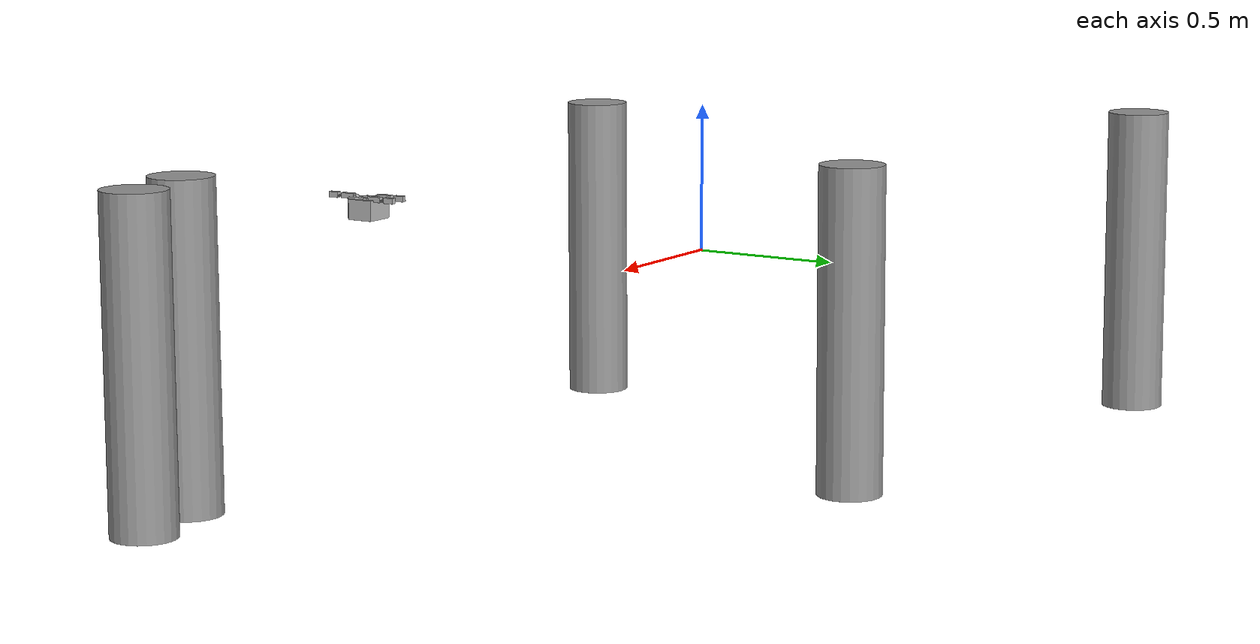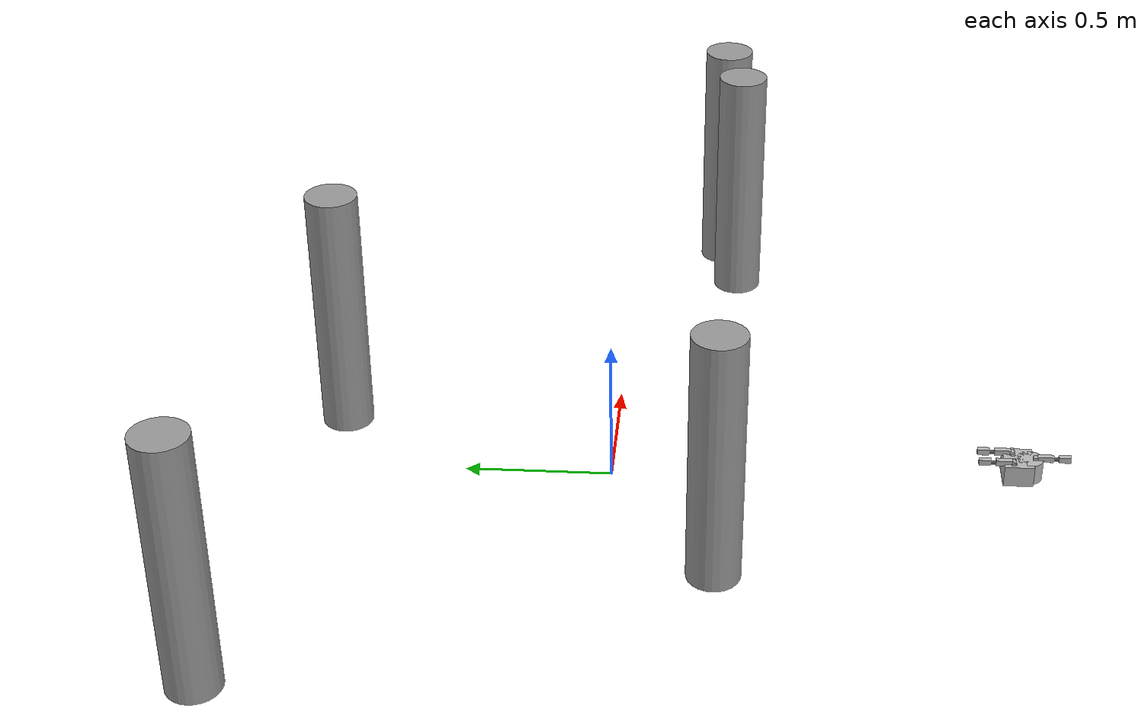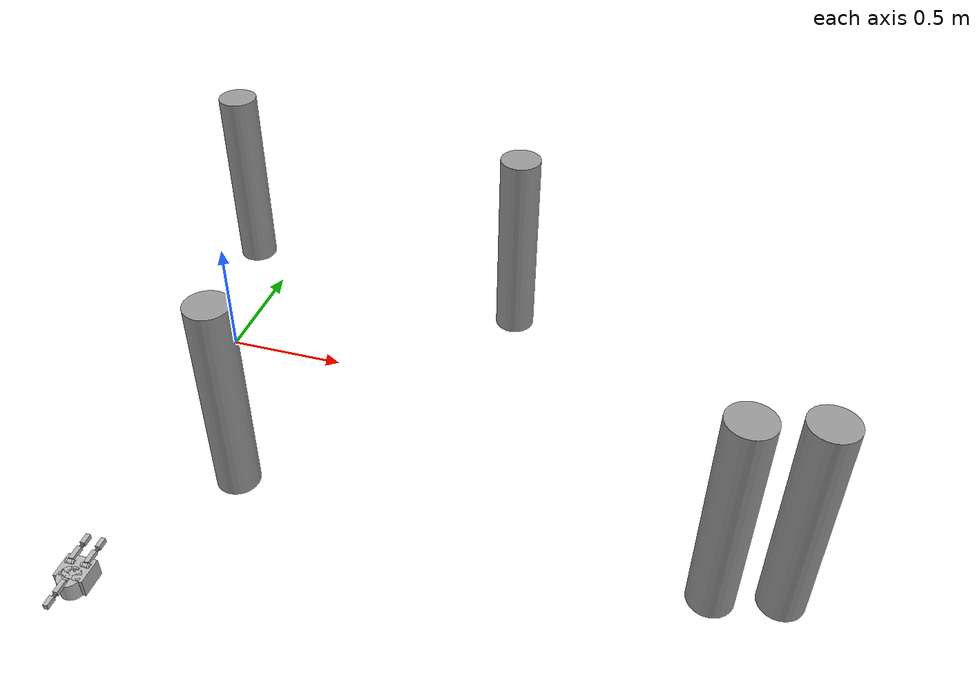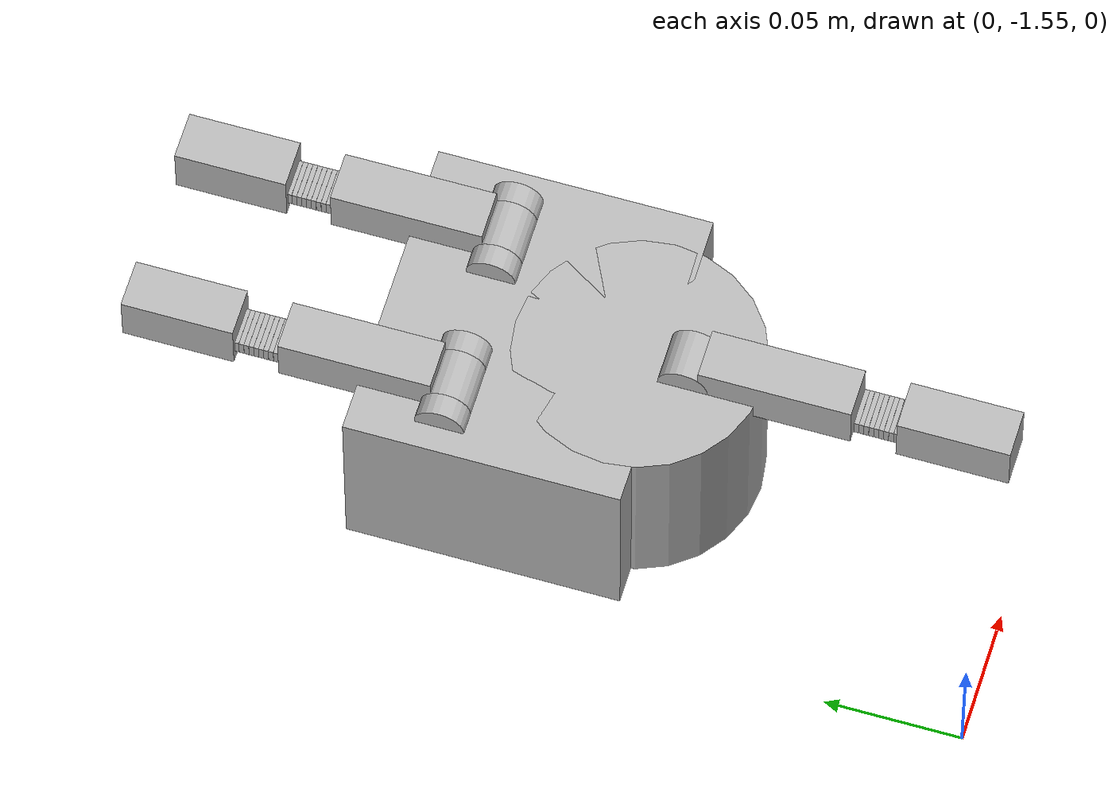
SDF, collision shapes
<?xml version='1.0'?>
<sdf version='1.7'>
  <model name='custom_Number_Around_World'>
    <link name='link'>
      <inertial>
        <mass>1</mass>
        <inertia>
          <ixx>0.145833</ixx>
          <ixy>0</ixy>
          <ixz>0</ixz>
          <iyy>0.145833</iyy>
          <iyz>0</iyz>
          <izz>0.125</izz>
        </inertia>
        <pose>0 0 0 0 -0 0</pose>
      </inertial>
      <self_collide>0</self_collide>
      <enable_wind>0</enable_wind>
      <kinematic>0</kinematic>
      <pose>0.114021 -0.353481 0 0 -0 0</pose>
      <gravity>1</gravity>
      <visual name='visual'>
        <geometry>
          <cylinder>
            <radius>0.1</radius>
            <length>1</length>
          </cylinder>
        </geometry>
        <material>
          <script>
            <name>Gazebo/Grey</name>
            <uri>file://media/materials/scripts/gazebo.material</uri>
          </script>
          <shader type='pixel'>
            <normal_map>__default__</normal_map>
          </shader>
          <ambient>0.3 0.3 0.3 1</ambient>
          <diffuse>0.7 0.7 0.7 1</diffuse>
          <specular>0.01 0.01 0.01 1</specular>
          <emissive>0 0 0 1</emissive>
        </material>
        <pose>0 0 0 0 -0 0</pose>
        <transparency>0</transparency>
        <cast_shadows>1</cast_shadows>
      </visual>
      <collision name='collision'>
        <laser_retro>0</laser_retro>
        <max_contacts>10</max_contacts>
        <pose>0 0 0 0 -0 0</pose>
        <geometry>
          <cylinder>
            <radius>0.1</radius>
            <length>1</length>
          </cylinder>
        </geometry>
        <surface>
          <friction>
            <ode>
              <mu>1</mu>
              <mu2>1</mu2>
              <fdir1>0 0 0</fdir1>
              <slip1>0</slip1>
              <slip2>0</slip2>
            </ode>
            <torsional>
              <coefficient>1</coefficient>
              <patch_radius>0</patch_radius>
              <surface_radius>0</surface_radius>
              <use_patch_radius>1</use_patch_radius>
              <ode>
                <slip>0</slip>
              </ode>
            </torsional>
          </friction>
          <bounce>
            <restitution_coefficient>0</restitution_coefficient>
            <threshold>1e+06</threshold>
          </bounce>
          <contact>
            <collide_without_contact>0</collide_without_contact>
            <collide_without_contact_bitmask>1</collide_without_contact_bitmask>
            <collide_bitmask>1</collide_bitmask>
            <ode>
              <soft_cfm>0</soft_cfm>
              <soft_erp>0.2</soft_erp>
              <kp>1e+13</kp>
              <kd>1</kd>
              <max_vel>0.01</max_vel>
              <min_depth>0</min_depth>
            </ode>
            <bullet>
              <split_impulse>1</split_impulse>
              <split_impulse_penetration_threshold>-0.01</split_impulse_penetration_threshold>
              <soft_cfm>0</soft_cfm>
              <soft_erp>0.2</soft_erp>
              <kp>1e+13</kp>
              <kd>1</kd>
            </bullet>
          </contact>
        </surface>
      </collision>
    </link>
    <link name='link_clone'>
      <inertial>
        <mass>1</mass>
        <inertia>
          <ixx>0.145833</ixx>
          <ixy>0</ixy>
          <ixz>0</ixz>
          <iyy>0.145833</iyy>
          <iyz>0</iyz>
          <izz>0.125</izz>
        </inertia>
        <pose>0 0 0 0 -0 0</pose>
      </inertial>
      <self_collide>0</self_collide>
      <enable_wind>0</enable_wind>
      <kinematic>0</kinematic>
      <pose>-0.593607 1.34719 -7e-06 -3e-06 -4e-06 -0</pose>
      <gravity>1</gravity>
      <visual name='visual'>
        <geometry>
          <cylinder>
            <radius>0.1</radius>
            <length>1</length>
          </cylinder>
        </geometry>
        <material>
          <script>
            <name>Gazebo/Grey</name>
            <uri>file://media/materials/scripts/gazebo.material</uri>
          </script>
          <shader type='pixel'>
            <normal_map>__default__</normal_map>
          </shader>
          <ambient>0.3 0.3 0.3 1</ambient>
          <diffuse>0.7 0.7 0.7 1</diffuse>
          <specular>0.01 0.01 0.01 1</specular>
          <emissive>0 0 0 1</emissive>
        </material>
        <pose>0 0 0 0 -0 0</pose>
        <transparency>0</transparency>
        <cast_shadows>1</cast_shadows>
      </visual>
      <collision name='collision'>
        <laser_retro>0</laser_retro>
        <max_contacts>10</max_contacts>
        <pose>0 0 0 0 -0 0</pose>
        <geometry>
          <cylinder>
            <radius>0.1</radius>
            <length>1</length>
          </cylinder>
        </geometry>
        <surface>
          <friction>
            <ode>
              <mu>1</mu>
              <mu2>1</mu2>
              <fdir1>0 0 0</fdir1>
              <slip1>0</slip1>
              <slip2>0</slip2>
            </ode>
            <torsional>
              <coefficient>1</coefficient>
              <patch_radius>0</patch_radius>
              <surface_radius>0</surface_radius>
              <use_patch_radius>1</use_patch_radius>
              <ode>
                <slip>0</slip>
              </ode>
            </torsional>
          </friction>
          <bounce>
            <restitution_coefficient>0</restitution_coefficient>
            <threshold>1e+06</threshold>
          </bounce>
          <contact>
            <collide_without_contact>0</collide_without_contact>
            <collide_without_contact_bitmask>1</collide_without_contact_bitmask>
            <collide_bitmask>1</collide_bitmask>
            <ode>
              <soft_cfm>0</soft_cfm>
              <soft_erp>0.2</soft_erp>
              <kp>1e+13</kp>
              <kd>1</kd>
              <max_vel>0.01</max_vel>
              <min_depth>0</min_depth>
            </ode>
            <bullet>
              <split_impulse>1</split_impulse>
              <split_impulse_penetration_threshold>-0.01</split_impulse_penetration_threshold>
              <soft_cfm>0</soft_cfm>
              <soft_erp>0.2</soft_erp>
              <kp>1e+13</kp>
              <kd>1</kd>
            </bullet>
          </contact>
        </surface>
      </collision>
    </link>
    <link name='link_clone_0'>
      <inertial>
        <mass>1</mass>
        <inertia>
          <ixx>0.145833</ixx>
          <ixy>0</ixy>
          <ixz>0</ixz>
          <iyy>0.145833</iyy>
          <iyz>0</iyz>
          <izz>0.125</izz>
        </inertia>
        <pose>0 0 0 0 -0 0</pose>
      </inertial>
      <self_collide>0</self_collide>
      <enable_wind>0</enable_wind>
      <kinematic>0</kinematic>
      <pose>2.52517 -0.335268 1.1e-05 -3e-06 -4e-06 -0</pose>
      <gravity>1</gravity>
      <visual name='visual'>
        <geometry>
          <cylinder>
            <radius>0.1</radius>
            <length>1</length>
          </cylinder>
        </geometry>
        <material>
          <script>
            <name>Gazebo/Grey</name>
            <uri>file://media/materials/scripts/gazebo.material</uri>
          </script>
          <shader type='pixel'>
            <normal_map>__default__</normal_map>
          </shader>
          <ambient>0.3 0.3 0.3 1</ambient>
          <diffuse>0.7 0.7 0.7 1</diffuse>
          <specular>0.01 0.01 0.01 1</specular>
          <emissive>0 0 0 1</emissive>
        </material>
        <pose>0 0 0 0 -0 0</pose>
        <transparency>0</transparency>
        <cast_shadows>1</cast_shadows>
      </visual>
      <collision name='collision'>
        <laser_retro>0</laser_retro>
        <max_contacts>10</max_contacts>
        <pose>0 0 0 0 -0 0</pose>
        <geometry>
          <cylinder>
            <radius>0.1</radius>
            <length>1</length>
          </cylinder>
        </geometry>
        <surface>
          <friction>
            <ode>
              <mu>1</mu>
              <mu2>1</mu2>
              <fdir1>0 0 0</fdir1>
              <slip1>0</slip1>
              <slip2>0</slip2>
            </ode>
            <torsional>
              <coefficient>1</coefficient>
              <patch_radius>0</patch_radius>
              <surface_radius>0</surface_radius>
              <use_patch_radius>1</use_patch_radius>
              <ode>
                <slip>0</slip>
              </ode>
            </torsional>
          </friction>
          <bounce>
            <restitution_coefficient>0</restitution_coefficient>
            <threshold>1e+06</threshold>
          </bounce>
          <contact>
            <collide_without_contact>0</collide_without_contact>
            <collide_without_contact_bitmask>1</collide_without_contact_bitmask>
            <collide_bitmask>1</collide_bitmask>
            <ode>
              <soft_cfm>0</soft_cfm>
              <soft_erp>0.2</soft_erp>
              <kp>1e+13</kp>
              <kd>1</kd>
              <max_vel>0.01</max_vel>
              <min_depth>0</min_depth>
            </ode>
            <bullet>
              <split_impulse>1</split_impulse>
              <split_impulse_penetration_threshold>-0.01</split_impulse_penetration_threshold>
              <soft_cfm>0</soft_cfm>
              <soft_erp>0.2</soft_erp>
              <kp>1e+13</kp>
              <kd>1</kd>
            </bullet>
          </contact>
        </surface>
      </collision>
    </link>
    <link name='link_clone_clone'>
      <inertial>
        <mass>1</mass>
        <inertia>
          <ixx>0.145833</ixx>
          <ixy>0</ixy>
          <ixz>0</ixz>
          <iyy>0.145833</iyy>
          <iyz>0</iyz>
          <izz>0.125</izz>
        </inertia>
        <pose>0 0 0 0 -0 0</pose>
      </inertial>
      <self_collide>0</self_collide>
      <enable_wind>0</enable_wind>
      <kinematic>0</kinematic>
      <pose>1.03311 1.13542 -7e-06 -6e-06 -8e-06 0</pose>
      <gravity>1</gravity>
      <visual name='visual'>
        <geometry>
          <cylinder>
            <radius>0.1</radius>
            <length>1</length>
          </cylinder>
        </geometry>
        <material>
          <script>
            <name>Gazebo/Grey</name>
            <uri>file://media/materials/scripts/gazebo.material</uri>
          </script>
          <shader type='pixel'>
            <normal_map>__default__</normal_map>
          </shader>
          <ambient>0.3 0.3 0.3 1</ambient>
          <diffuse>0.7 0.7 0.7 1</diffuse>
          <specular>0.01 0.01 0.01 1</specular>
          <emissive>0 0 0 1</emissive>
        </material>
        <pose>0 0 0 0 -0 0</pose>
        <transparency>0</transparency>
        <cast_shadows>1</cast_shadows>
      </visual>
      <collision name='collision'>
        <laser_retro>0</laser_retro>
        <max_contacts>10</max_contacts>
        <pose>0 0 0 0 -0 0</pose>
        <geometry>
          <cylinder>
            <radius>0.1</radius>
            <length>1</length>
          </cylinder>
        </geometry>
        <surface>
          <friction>
            <ode>
              <mu>1</mu>
              <mu2>1</mu2>
              <fdir1>0 0 0</fdir1>
              <slip1>0</slip1>
              <slip2>0</slip2>
            </ode>
            <torsional>
              <coefficient>1</coefficient>
              <patch_radius>0</patch_radius>
              <surface_radius>0</surface_radius>
              <use_patch_radius>1</use_patch_radius>
              <ode>
                <slip>0</slip>
              </ode>
            </torsional>
          </friction>
          <bounce>
            <restitution_coefficient>0</restitution_coefficient>
            <threshold>1e+06</threshold>
          </bounce>
          <contact>
            <collide_without_contact>0</collide_without_contact>
            <collide_without_contact_bitmask>1</collide_without_contact_bitmask>
            <collide_bitmask>1</collide_bitmask>
            <ode>
              <soft_cfm>0</soft_cfm>
              <soft_erp>0.2</soft_erp>
              <kp>1e+13</kp>
              <kd>1</kd>
              <max_vel>0.01</max_vel>
              <min_depth>0</min_depth>
            </ode>
            <bullet>
              <split_impulse>1</split_impulse>
              <split_impulse_penetration_threshold>-0.01</split_impulse_penetration_threshold>
              <soft_cfm>0</soft_cfm>
              <soft_erp>0.2</soft_erp>
              <kp>1e+13</kp>
              <kd>1</kd>
            </bullet>
          </contact>
        </surface>
      </collision>
    </link>
    <link name='link_clone_clone_0'>
      <inertial>
        <mass>1</mass>
        <inertia>
          <ixx>0.145833</ixx>
          <ixy>0</ixy>
          <ixz>0</ixz>
          <iyy>0.145833</iyy>
          <iyz>0</iyz>
          <izz>0.125</izz>
        </inertia>
        <pose>0 0 0 0 -0 0</pose>
      </inertial>
      <self_collide>0</self_collide>
      <enable_wind>0</enable_wind>
      <kinematic>0</kinematic>
      <pose>2.24794 -0.400036 5e-06 -6e-06 -8e-06 0</pose>
      <gravity>1</gravity>
      <visual name='visual'>
        <geometry>
          <cylinder>
            <radius>0.1</radius>
            <length>1</length>
          </cylinder>
        </geometry>
        <material>
          <script>
            <name>Gazebo/Grey</name>
            <uri>file://media/materials/scripts/gazebo.material</uri>
          </script>
          <shader type='pixel'>
            <normal_map>__default__</normal_map>
          </shader>
          <ambient>0.3 0.3 0.3 1</ambient>
          <diffuse>0.7 0.7 0.7 1</diffuse>
          <specular>0.01 0.01 0.01 1</specular>
          <emissive>0 0 0 1</emissive>
        </material>
        <pose>0 0 0 0 -0 0</pose>
        <transparency>0</transparency>
        <cast_shadows>1</cast_shadows>
      </visual>
      <collision name='collision'>
        <laser_retro>0</laser_retro>
        <max_contacts>10</max_contacts>
        <pose>0 0 0 0 -0 0</pose>
        <geometry>
          <cylinder>
            <radius>0.1</radius>
            <length>1</length>
          </cylinder>
        </geometry>
        <surface>
          <friction>
            <ode>
              <mu>1</mu>
              <mu2>1</mu2>
              <fdir1>0 0 0</fdir1>
              <slip1>0</slip1>
              <slip2>0</slip2>
            </ode>
            <torsional>
              <coefficient>1</coefficient>
              <patch_radius>0</patch_radius>
              <surface_radius>0</surface_radius>
              <use_patch_radius>1</use_patch_radius>
              <ode>
                <slip>0</slip>
              </ode>
            </torsional>
          </friction>
          <bounce>
            <restitution_coefficient>0</restitution_coefficient>
            <threshold>1e+06</threshold>
          </bounce>
          <contact>
            <collide_without_contact>0</collide_without_contact>
            <collide_without_contact_bitmask>1</collide_without_contact_bitmask>
            <collide_bitmask>1</collide_bitmask>
            <ode>
              <soft_cfm>0</soft_cfm>
              <soft_erp>0.2</soft_erp>
              <kp>1e+13</kp>
              <kd>1</kd>
              <max_vel>0.01</max_vel>
              <min_depth>0</min_depth>
            </ode>
            <bullet>
              <split_impulse>1</split_impulse>
              <split_impulse_penetration_threshold>-0.01</split_impulse_penetration_threshold>
              <soft_cfm>0</soft_cfm>
              <soft_erp>0.2</soft_erp>
              <kp>1e+13</kp>
              <kd>1</kd>
            </bullet>
          </contact>
        </surface>
      </collision>
    </link>
    <model name='irobot_hand'>
      <static>0</static>
      <link name='base_link'>
        <inertial>
          <mass>0.1</mass>
          <inertia>
            <ixx>0.001</ixx>
            <ixy>0</ixy>
            <ixz>0</ixz>
            <iyy>0.001</iyy>
            <iyz>0</iyz>
            <izz>0.001</izz>
          </inertia>
        </inertial>
        <collision name='collision1'>
          <pose>0 0.02 0.045 0 -0 0</pose>
          <geometry>
            <box>
              <size>0.114 0.1 0.075</size>
            </box>
          </geometry>
        </collision>
        <collision name='collision2'>
          <pose>0 -0.02 0.045 0 -0 0</pose>
          <geometry>
            <cylinder>
              <radius>0.0448</radius>
              <length>0.075</length>
            </cylinder>
          </geometry>
        </collision>
        <visual name='base_link_vis'>
          <pose>0 -0.038 -0.023 0 -0 0</pose>
          <geometry>
            <mesh>
              <uri>model://irobot_hand/meshes/palm.stl</uri>
            </mesh>
          </geometry>
        </visual>
      </link>
      <link name='finger0/base_rotation_link'>
        <pose>0.03075 0.038 0.069477 0 -0 0</pose>
        <inertial>
          <mass>0.1</mass>
          <inertia>
            <ixx>0.001</ixx>
            <ixy>0</ixy>
            <ixz>0</ixz>
            <iyy>0.001</iyy>
            <iyz>0</iyz>
            <izz>0.001</izz>
          </inertia>
        </inertial>
        <collision name='collision_1'>
          <pose>0 0 -0.0025 0 -0 0</pose>
          <geometry>
            <cylinder>
              <length>0.0145</length>
              <radius>0.025</radius>
            </cylinder>
          </geometry>
        </collision>
        <collision name='collision_2'>
          <pose>0 0 -0.0104 0 -0 0</pose>
          <geometry>
            <cylinder>
              <length>0.0145</length>
              <radius>0.0165</radius>
            </cylinder>
          </geometry>
        </collision>
        <collision name='collision_3'>
          <pose>0 0 0.0135 1.5707 0 1.5707</pose>
          <geometry>
            <cylinder>
              <length>0.02</length>
              <radius>0.002</radius>
            </cylinder>
          </geometry>
        </collision>
        <collision name='collision_4'>
          <pose>0.013 0 0.0135 1.5707 0 1.5707</pose>
          <geometry>
            <cylinder>
              <length>0.008</length>
              <radius>0.009</radius>
            </cylinder>
          </geometry>
        </collision>
        <collision name='collision_5'>
          <pose>-0.013 0 0.0135 1.5707 0 1.5707</pose>
          <geometry>
            <cylinder>
              <length>0.008</length>
              <radius>0.009</radius>
            </cylinder>
          </geometry>
        </collision>
        <visual name='finger0/base_rotation_link_vis'>
          <pose>0 0 0 1.57 -0 0</pose>
          <geometry>
            <mesh>
              <uri>model://irobot_hand/meshes/finger_base.stl</uri>
            </mesh>
          </geometry>
        </visual>
      </link>
      <link name='finger0/proximal_link'>
        <pose>0.03075 0.038 0.082977 1.57 -0 -3.14</pose>
        <inertial>
          <mass>0.1</mass>
          <inertia>
            <ixx>0.001</ixx>
            <ixy>0</ixy>
            <ixz>0</ixz>
            <iyy>0.001</iyy>
            <iyz>0</iyz>
            <izz>0.001</izz>
          </inertia>
        </inertial>
        <collision name='collision1'>
          <pose>0 0.0028 0.033 0 -0 0</pose>
          <geometry>
            <box>
              <size>0.018 0.019 0.055</size>
            </box>
          </geometry>
        </collision>
        <collision name='collision2'>
          <pose>0 0 0 0 1.5707 0</pose>
          <geometry>
            <cylinder>
              <radius>0.009</radius>
              <length>0.018</length>
            </cylinder>
          </geometry>
        </collision>
        <visual name='visual'>
          <pose>0 0 0 1.57 -1.57 -0</pose>
          <geometry>
            <mesh>
              <uri>model://irobot_hand/meshes/finger_proximal.stl</uri>
            </mesh>
          </geometry>
        </visual>
      </link>
      <link name='finger0/flexible_link_hidden_between_proximal_link_and_1'>
        <pose>0.030651 0.1 0.083026 1.57 -0 -3.14</pose>
        <inertial>
          <mass>0.1</mass>
          <inertia>
            <ixx>0.001</ixx>
            <ixy>0</ixy>
            <ixz>0</ixz>
            <iyy>0.001</iyy>
            <iyz>0</iyz>
            <izz>0.001</izz>
          </inertia>
        </inertial>
      </link>
      <link name='finger0/flexible_link_1'>
        <pose>0.030651 0.1 0.083026 1.57 -0 -3.14</pose>
        <inertial>
          <mass>0.1</mass>
          <inertia>
            <ixx>0.001</ixx>
            <ixy>0</ixy>
            <ixz>0</ixz>
            <iyy>0.001</iyy>
            <iyz>0</iyz>
            <izz>0.001</izz>
          </inertia>
        </inertial>
        <collision name='collision'>
          <pose>0 0 0 1.57 -0 0</pose>
          <geometry>
            <box>
              <size>0.014 0.00176 0.006</size>
            </box>
          </geometry>
        </collision>
        <visual name='visual'>
          <pose>0 0 0 1.57 -0 0</pose>
          <geometry>
            <box>
              <size>0.014 0.00176 0.006</size>
            </box>
          </geometry>
        </visual>
      </link>
      <link name='finger0/flexible_link_hidden_between_1_and_2'>
        <pose>0.030648 0.101778 0.083028 1.57 -0 -3.14</pose>
        <inertial>
          <mass>0.1</mass>
          <inertia>
            <ixx>0.001</ixx>
            <ixy>0</ixy>
            <ixz>0</ixz>
            <iyy>0.001</iyy>
            <iyz>0</iyz>
            <izz>0.001</izz>
          </inertia>
        </inertial>
      </link>
      <link name='finger0/flexible_link_2'>
        <pose>0.030648 0.101778 0.083028 1.57 -0 -3.14</pose>
        <inertial>
          <mass>0.1</mass>
          <inertia>
            <ixx>0.001</ixx>
            <ixy>0</ixy>
            <ixz>0</ixz>
            <iyy>0.001</iyy>
            <iyz>0</iyz>
            <izz>0.001</izz>
          </inertia>
        </inertial>
        <collision name='collision'>
          <pose>0 0 0 1.57 -0 0</pose>
          <geometry>
            <box>
              <size>0.014 0.00176 0.006</size>
            </box>
          </geometry>
        </collision>
        <visual name='visual'>
          <pose>0 0 0 1.57 -0 0</pose>
          <geometry>
            <box>
              <size>0.014 0.00176 0.006</size>
            </box>
          </geometry>
        </visual>
      </link>
      <link name='finger0/flexible_link_hidden_between_2_and_3'>
        <pose>0.030646 0.103555 0.083029 1.57 -0 -3.14</pose>
        <inertial>
          <mass>0.1</mass>
          <inertia>
            <ixx>0.001</ixx>
            <ixy>0</ixy>
            <ixz>0</ixz>
            <iyy>0.001</iyy>
            <iyz>0</iyz>
            <izz>0.001</izz>
          </inertia>
        </inertial>
      </link>
      <link name='finger0/flexible_link_3'>
        <pose>0.030646 0.103555 0.083029 1.57 -0 -3.14</pose>
        <inertial>
          <mass>0.1</mass>
          <inertia>
            <ixx>0.001</ixx>
            <ixy>0</ixy>
            <ixz>0</ixz>
            <iyy>0.001</iyy>
            <iyz>0</iyz>
            <izz>0.001</izz>
          </inertia>
        </inertial>
        <collision name='collision'>
          <pose>0 0 0 1.57 -0 0</pose>
          <geometry>
            <box>
              <size>0.014 0.00176 0.006</size>
            </box>
          </geometry>
        </collision>
        <visual name='visual'>
          <pose>0 0 0 1.57 -0 0</pose>
          <geometry>
            <box>
              <size>0.014 0.00176 0.006</size>
            </box>
          </geometry>
        </visual>
      </link>
      <link name='finger0/flexible_link_hidden_between_3_and_4'>
        <pose>0.030643 0.105333 0.083031 1.57 -0 -3.14</pose>
        <inertial>
          <mass>0.1</mass>
          <inertia>
            <ixx>0.001</ixx>
            <ixy>0</ixy>
            <ixz>0</ixz>
            <iyy>0.001</iyy>
            <iyz>0</iyz>
            <izz>0.001</izz>
          </inertia>
        </inertial>
      </link>
      <link name='finger0/flexible_link_4'>
        <pose>0.030643 0.105333 0.083031 1.57 -0 -3.14</pose>
        <inertial>
          <mass>0.1</mass>
          <inertia>
            <ixx>0.001</ixx>
            <ixy>0</ixy>
            <ixz>0</ixz>
            <iyy>0.001</iyy>
            <iyz>0</iyz>
            <izz>0.001</izz>
          </inertia>
        </inertial>
        <collision name='collision'>
          <pose>0 0 0 1.57 -0 0</pose>
          <geometry>
            <box>
              <size>0.014 0.00176 0.006</size>
            </box>
          </geometry>
        </collision>
        <visual name='visual'>
          <pose>0 0 0 1.57 -0 0</pose>
          <geometry>
            <box>
              <size>0.014 0.00176 0.006</size>
            </box>
          </geometry>
        </visual>
      </link>
      <link name='finger0/flexible_link_hidden_between_4_and_5'>
        <pose>0.03064 0.107111 0.083032 1.57 -0 -3.14</pose>
        <inertial>
          <mass>0.1</mass>
          <inertia>
            <ixx>0.001</ixx>
            <ixy>0</ixy>
            <ixz>0</ixz>
            <iyy>0.001</iyy>
            <iyz>0</iyz>
            <izz>0.001</izz>
          </inertia>
        </inertial>
      </link>
      <link name='finger0/flexible_link_5'>
        <pose>0.03064 0.107111 0.083032 1.57 -0 -3.14</pose>
        <inertial>
          <mass>0.1</mass>
          <inertia>
            <ixx>0.001</ixx>
            <ixy>0</ixy>
            <ixz>0</ixz>
            <iyy>0.001</iyy>
            <iyz>0</iyz>
            <izz>0.001</izz>
          </inertia>
        </inertial>
        <collision name='collision'>
          <pose>0 0 0 1.57 -0 0</pose>
          <geometry>
            <box>
              <size>0.014 0.00176 0.006</size>
            </box>
          </geometry>
        </collision>
        <visual name='visual'>
          <pose>0 0 0 1.57 -0 0</pose>
          <geometry>
            <box>
              <size>0.014 0.00176 0.006</size>
            </box>
          </geometry>
        </visual>
      </link>
      <link name='finger0/flexible_link_hidden_between_5_and_6'>
        <pose>0.030637 0.108889 0.083033 1.57 -0 -3.14</pose>
        <inertial>
          <mass>0.1</mass>
          <inertia>
            <ixx>0.001</ixx>
            <ixy>0</ixy>
            <ixz>0</ixz>
            <iyy>0.001</iyy>
            <iyz>0</iyz>
            <izz>0.001</izz>
          </inertia>
        </inertial>
      </link>
      <link name='finger0/flexible_link_6'>
        <pose>0.030637 0.108889 0.083033 1.57 -0 -3.14</pose>
        <inertial>
          <mass>0.1</mass>
          <inertia>
            <ixx>0.001</ixx>
            <ixy>0</ixy>
            <ixz>0</ixz>
            <iyy>0.001</iyy>
            <iyz>0</iyz>
            <izz>0.001</izz>
          </inertia>
        </inertial>
        <collision name='collision'>
          <pose>0 0 0 1.57 -0 0</pose>
          <geometry>
            <box>
              <size>0.014 0.00176 0.006</size>
            </box>
          </geometry>
        </collision>
        <visual name='visual'>
          <pose>0 0 0 1.57 -0 0</pose>
          <geometry>
            <box>
              <size>0.014 0.00176 0.006</size>
            </box>
          </geometry>
        </visual>
      </link>
      <link name='finger0/flexible_link_hidden_between_6_and_7'>
        <pose>0.030634 0.110667 0.083035 1.57 -0 -3.14</pose>
        <inertial>
          <mass>0.1</mass>
          <inertia>
            <ixx>0.001</ixx>
            <ixy>0</ixy>
            <ixz>0</ixz>
            <iyy>0.001</iyy>
            <iyz>0</iyz>
            <izz>0.001</izz>
          </inertia>
        </inertial>
      </link>
      <link name='finger0/flexible_link_7'>
        <pose>0.030634 0.110667 0.083035 1.57 -0 -3.14</pose>
        <inertial>
          <mass>0.1</mass>
          <inertia>
            <ixx>0.001</ixx>
            <ixy>0</ixy>
            <ixz>0</ixz>
            <iyy>0.001</iyy>
            <iyz>0</iyz>
            <izz>0.001</izz>
          </inertia>
        </inertial>
        <collision name='collision'>
          <pose>0 0 0 1.57 -0 0</pose>
          <geometry>
            <box>
              <size>0.014 0.00176 0.006</size>
            </box>
          </geometry>
        </collision>
        <visual name='visual'>
          <pose>0 0 0 1.57 -0 0</pose>
          <geometry>
            <box>
              <size>0.014 0.00176 0.006</size>
            </box>
          </geometry>
        </visual>
      </link>
      <link name='finger0/flexible_link_hidden_between_7_and_8'>
        <pose>0.030631 0.112444 0.083036 1.57 -0 -3.14</pose>
        <inertial>
          <mass>0.1</mass>
          <inertia>
            <ixx>0.001</ixx>
            <ixy>0</ixy>
            <ixz>0</ixz>
            <iyy>0.001</iyy>
            <iyz>0</iyz>
            <izz>0.001</izz>
          </inertia>
        </inertial>
      </link>
      <link name='finger0/flexible_link_8'>
        <pose>0.030631 0.112444 0.083036 1.57 -0 -3.14</pose>
        <inertial>
          <mass>0.1</mass>
          <inertia>
            <ixx>0.001</ixx>
            <ixy>0</ixy>
            <ixz>0</ixz>
            <iyy>0.001</iyy>
            <iyz>0</iyz>
            <izz>0.001</izz>
          </inertia>
        </inertial>
        <collision name='collision'>
          <pose>0 0 0 1.57 -0 0</pose>
          <geometry>
            <box>
              <size>0.014 0.00176 0.006</size>
            </box>
          </geometry>
        </collision>
        <visual name='visual'>
          <pose>0 0 0 1.57 -0 0</pose>
          <geometry>
            <box>
              <size>0.014 0.00176 0.006</size>
            </box>
          </geometry>
        </visual>
      </link>
      <link name='finger0/flexible_link_hidden_between_8_and_9'>
        <pose>0.030629 0.114222 0.083038 1.57 -0 -3.14</pose>
        <inertial>
          <mass>0.1</mass>
          <inertia>
            <ixx>0.001</ixx>
            <ixy>0</ixy>
            <ixz>0</ixz>
            <iyy>0.001</iyy>
            <iyz>0</iyz>
            <izz>0.001</izz>
          </inertia>
        </inertial>
      </link>
      <link name='finger0/flexible_link_9'>
        <pose>0.030629 0.114222 0.083038 1.57 -0 -3.14</pose>
        <inertial>
          <mass>0.1</mass>
          <inertia>
            <ixx>0.001</ixx>
            <ixy>0</ixy>
            <ixz>0</ixz>
            <iyy>0.001</iyy>
            <iyz>0</iyz>
            <izz>0.001</izz>
          </inertia>
        </inertial>
        <collision name='collision'>
          <pose>0 0 0 1.57 -0 0</pose>
          <geometry>
            <box>
              <size>0.014 0.00176 0.006</size>
            </box>
          </geometry>
        </collision>
        <visual name='visual'>
          <pose>0 0 0 1.57 -0 0</pose>
          <geometry>
            <box>
              <size>0.014 0.00176 0.006</size>
            </box>
          </geometry>
        </visual>
      </link>
      <link name='finger0/flexible_link_hidden_between_9_and_distal_link'>
        <pose>0.030626 0.116 0.083039 1.57 -0 -3.14</pose>
        <inertial>
          <mass>0.1</mass>
          <inertia>
            <ixx>0.001</ixx>
            <ixy>0</ixy>
            <ixz>0</ixz>
            <iyy>0.001</iyy>
            <iyz>0</iyz>
            <izz>0.001</izz>
          </inertia>
        </inertial>
      </link>
      <link name='finger0/distal_link'>
        <pose>0.030626 0.116 0.083039 1.57 -0 -3.14</pose>
        <inertial>
          <mass>0.1</mass>
          <inertia>
            <ixx>0.001</ixx>
            <ixy>0</ixy>
            <ixz>0</ixz>
            <iyy>0.001</iyy>
            <iyz>0</iyz>
            <izz>0.001</izz>
          </inertia>
        </inertial>
        <collision name='collision'>
          <pose>0 0.0025 0.019 3.14159 0.001593 3.14159</pose>
          <geometry>
            <box>
              <size>0.0175 0.02023 0.04043</size>
            </box>
          </geometry>
        </collision>
        <visual name='visual'>
          <pose>0 0 0 3.14159 0.001593 3.14159</pose>
          <geometry>
            <mesh>
              <uri>model://irobot_hand/meshes/finger_distal.stl</uri>
            </mesh>
          </geometry>
        </visual>
      </link>
      <link name='finger1/base_rotation_link'>
        <pose>-0.03075 0.038 0.069477 0 -0 0</pose>
        <inertial>
          <mass>0.1</mass>
          <inertia>
            <ixx>0.001</ixx>
            <ixy>0</ixy>
            <ixz>0</ixz>
            <iyy>0.001</iyy>
            <iyz>0</iyz>
            <izz>0.001</izz>
          </inertia>
        </inertial>
        <collision name='collision_1'>
          <pose>0 0 -0.0025 0 -0 0</pose>
          <geometry>
            <cylinder>
              <length>0.0145</length>
              <radius>0.025</radius>
            </cylinder>
          </geometry>
        </collision>
        <collision name='collision_2'>
          <pose>0 0 -0.0104 0 -0 0</pose>
          <geometry>
            <cylinder>
              <length>0.0145</length>
              <radius>0.0165</radius>
            </cylinder>
          </geometry>
        </collision>
        <collision name='collision_3'>
          <pose>0 0 0.0135 1.5707 0 1.5707</pose>
          <geometry>
            <cylinder>
              <length>0.02</length>
              <radius>0.002</radius>
            </cylinder>
          </geometry>
        </collision>
        <collision name='collision_4'>
          <pose>0.013 0 0.0135 1.5707 0 1.5707</pose>
          <geometry>
            <cylinder>
              <length>0.008</length>
              <radius>0.009</radius>
            </cylinder>
          </geometry>
        </collision>
        <collision name='collision_5'>
          <pose>-0.013 0 0.0135 1.5707 0 1.5707</pose>
          <geometry>
            <cylinder>
              <length>0.008</length>
              <radius>0.009</radius>
            </cylinder>
          </geometry>
        </collision>
        <visual name='visual'>
          <pose>0 0 0 1.57 -0 0</pose>
          <geometry>
            <mesh>
              <uri>model://irobot_hand/meshes/finger_base.stl</uri>
            </mesh>
          </geometry>
        </visual>
      </link>
      <link name='finger1/proximal_link'>
        <pose>-0.03075 0.038 0.082977 1.57 -0 -3.14</pose>
        <inertial>
          <mass>0.1</mass>
          <inertia>
            <ixx>0.001</ixx>
            <ixy>0</ixy>
            <ixz>0</ixz>
            <iyy>0.001</iyy>
            <iyz>0</iyz>
            <izz>0.001</izz>
          </inertia>
        </inertial>
        <collision name='collision1'>
          <pose>0 0.0028 0.033 0 -0 0</pose>
          <geometry>
            <box>
              <size>0.018 0.019 0.055</size>
            </box>
          </geometry>
        </collision>
        <collision name='collision2'>
          <pose>0 0 0 0 1.5707 0</pose>
          <geometry>
            <cylinder>
              <radius>0.009</radius>
              <length>0.018</length>
            </cylinder>
          </geometry>
        </collision>
        <visual name='visual'>
          <pose>0 0 0 1.57 -1.57 -0</pose>
          <geometry>
            <mesh>
              <uri>model://irobot_hand/meshes/finger_proximal.stl</uri>
            </mesh>
          </geometry>
        </visual>
      </link>
      <link name='finger1/flexible_link_hidden_between_proximal_link_and_1'>
        <pose>-0.030849 0.1 0.083026 1.57 -0 -3.14</pose>
        <inertial>
          <mass>0.1</mass>
          <inertia>
            <ixx>0.001</ixx>
            <ixy>0</ixy>
            <ixz>0</ixz>
            <iyy>0.001</iyy>
            <iyz>0</iyz>
            <izz>0.001</izz>
          </inertia>
        </inertial>
      </link>
      <link name='finger1/flexible_link_1'>
        <pose>-0.030849 0.1 0.083026 1.57 -0 -3.14</pose>
        <inertial>
          <mass>0.1</mass>
          <inertia>
            <ixx>0.001</ixx>
            <ixy>0</ixy>
            <ixz>0</ixz>
            <iyy>0.001</iyy>
            <iyz>0</iyz>
            <izz>0.001</izz>
          </inertia>
        </inertial>
        <collision name='collision'>
          <pose>0 0 0 1.57 -0 0</pose>
          <geometry>
            <box>
              <size>0.014 0.00176 0.006</size>
            </box>
          </geometry>
        </collision>
        <visual name='visual'>
          <pose>0 0 0 1.57 -0 0</pose>
          <geometry>
            <box>
              <size>0.014 0.00176 0.006</size>
            </box>
          </geometry>
        </visual>
      </link>
      <link name='finger1/flexible_link_hidden_between_1_and_2'>
        <pose>-0.030852 0.101778 0.083028 1.57 -0 -3.14</pose>
        <inertial>
          <mass>0.1</mass>
          <inertia>
            <ixx>0.001</ixx>
            <ixy>0</ixy>
            <ixz>0</ixz>
            <iyy>0.001</iyy>
            <iyz>0</iyz>
            <izz>0.001</izz>
          </inertia>
        </inertial>
      </link>
      <link name='finger1/flexible_link_2'>
        <pose>-0.030852 0.101778 0.083028 1.57 -0 -3.14</pose>
        <inertial>
          <mass>0.1</mass>
          <inertia>
            <ixx>0.001</ixx>
            <ixy>0</ixy>
            <ixz>0</ixz>
            <iyy>0.001</iyy>
            <iyz>0</iyz>
            <izz>0.001</izz>
          </inertia>
        </inertial>
        <collision name='collision'>
          <pose>0 0 0 1.57 -0 0</pose>
          <geometry>
            <box>
              <size>0.014 0.00176 0.006</size>
            </box>
          </geometry>
        </collision>
        <visual name='visual'>
          <pose>0 0 0 1.57 -0 0</pose>
          <geometry>
            <box>
              <size>0.014 0.00176 0.006</size>
            </box>
          </geometry>
        </visual>
      </link>
      <link name='finger1/flexible_link_hidden_between_2_and_3'>
        <pose>-0.030854 0.103555 0.083029 1.57 -0 -3.14</pose>
        <inertial>
          <mass>0.1</mass>
          <inertia>
            <ixx>0.001</ixx>
            <ixy>0</ixy>
            <ixz>0</ixz>
            <iyy>0.001</iyy>
            <iyz>0</iyz>
            <izz>0.001</izz>
          </inertia>
        </inertial>
      </link>
      <link name='finger1/flexible_link_3'>
        <pose>-0.030854 0.103555 0.083029 1.57 -0 -3.14</pose>
        <inertial>
          <mass>0.1</mass>
          <inertia>
            <ixx>0.001</ixx>
            <ixy>0</ixy>
            <ixz>0</ixz>
            <iyy>0.001</iyy>
            <iyz>0</iyz>
            <izz>0.001</izz>
          </inertia>
        </inertial>
        <collision name='collision'>
          <pose>0 0 0 1.57 -0 0</pose>
          <geometry>
            <box>
              <size>0.014 0.00176 0.006</size>
            </box>
          </geometry>
        </collision>
        <visual name='visual'>
          <pose>0 0 0 1.57 -0 0</pose>
          <geometry>
            <box>
              <size>0.014 0.00176 0.006</size>
            </box>
          </geometry>
        </visual>
      </link>
      <link name='finger1/flexible_link_hidden_between_3_and_4'>
        <pose>-0.030857 0.105333 0.083031 1.57 -0 -3.14</pose>
        <inertial>
          <mass>0.1</mass>
          <inertia>
            <ixx>0.001</ixx>
            <ixy>0</ixy>
            <ixz>0</ixz>
            <iyy>0.001</iyy>
            <iyz>0</iyz>
            <izz>0.001</izz>
          </inertia>
        </inertial>
      </link>
      <link name='finger1/flexible_link_4'>
        <pose>-0.030857 0.105333 0.083031 1.57 -0 -3.14</pose>
        <inertial>
          <mass>0.1</mass>
          <inertia>
            <ixx>0.001</ixx>
            <ixy>0</ixy>
            <ixz>0</ixz>
            <iyy>0.001</iyy>
            <iyz>0</iyz>
            <izz>0.001</izz>
          </inertia>
        </inertial>
        <collision name='collision'>
          <pose>0 0 0 1.57 -0 0</pose>
          <geometry>
            <box>
              <size>0.014 0.00176 0.006</size>
            </box>
          </geometry>
        </collision>
        <visual name='visual'>
          <pose>0 0 0 1.57 -0 0</pose>
          <geometry>
            <box>
              <size>0.014 0.00176 0.006</size>
            </box>
          </geometry>
        </visual>
      </link>
      <link name='finger1/flexible_link_hidden_between_4_and_5'>
        <pose>-0.03086 0.107111 0.083032 1.57 -0 -3.14</pose>
        <inertial>
          <mass>0.1</mass>
          <inertia>
            <ixx>0.001</ixx>
            <ixy>0</ixy>
            <ixz>0</ixz>
            <iyy>0.001</iyy>
            <iyz>0</iyz>
            <izz>0.001</izz>
          </inertia>
        </inertial>
      </link>
      <link name='finger1/flexible_link_5'>
        <pose>-0.03086 0.107111 0.083032 1.57 -0 -3.14</pose>
        <inertial>
          <mass>0.1</mass>
          <inertia>
            <ixx>0.001</ixx>
            <ixy>0</ixy>
            <ixz>0</ixz>
            <iyy>0.001</iyy>
            <iyz>0</iyz>
            <izz>0.001</izz>
          </inertia>
        </inertial>
        <collision name='collision'>
          <pose>0 0 0 1.57 -0 0</pose>
          <geometry>
            <box>
              <size>0.014 0.00176 0.006</size>
            </box>
          </geometry>
        </collision>
        <visual name='visual'>
          <pose>0 0 0 1.57 -0 0</pose>
          <geometry>
            <box>
              <size>0.014 0.00176 0.006</size>
            </box>
          </geometry>
        </visual>
      </link>
      <link name='finger1/flexible_link_hidden_between_5_and_6'>
        <pose>-0.030863 0.108889 0.083033 1.57 -0 -3.14</pose>
        <inertial>
          <mass>0.1</mass>
          <inertia>
            <ixx>0.001</ixx>
            <ixy>0</ixy>
            <ixz>0</ixz>
            <iyy>0.001</iyy>
            <iyz>0</iyz>
            <izz>0.001</izz>
          </inertia>
        </inertial>
      </link>
      <link name='finger1/flexible_link_6'>
        <pose>-0.030863 0.108889 0.083033 1.57 -0 -3.14</pose>
        <inertial>
          <mass>0.1</mass>
          <inertia>
            <ixx>0.001</ixx>
            <ixy>0</ixy>
            <ixz>0</ixz>
            <iyy>0.001</iyy>
            <iyz>0</iyz>
            <izz>0.001</izz>
          </inertia>
        </inertial>
        <collision name='collision'>
          <pose>0 0 0 1.57 -0 0</pose>
          <geometry>
            <box>
              <size>0.014 0.00176 0.006</size>
            </box>
          </geometry>
        </collision>
        <visual name='visual'>
          <pose>0 0 0 1.57 -0 0</pose>
          <geometry>
            <box>
              <size>0.014 0.00176 0.006</size>
            </box>
          </geometry>
        </visual>
      </link>
      <link name='finger1/flexible_link_hidden_between_6_and_7'>
        <pose>-0.030866 0.110667 0.083035 1.57 -0 -3.14</pose>
        <inertial>
          <mass>0.1</mass>
          <inertia>
            <ixx>0.001</ixx>
            <ixy>0</ixy>
            <ixz>0</ixz>
            <iyy>0.001</iyy>
            <iyz>0</iyz>
            <izz>0.001</izz>
          </inertia>
        </inertial>
      </link>
      <link name='finger1/flexible_link_7'>
        <pose>-0.030866 0.110667 0.083035 1.57 -0 -3.14</pose>
        <inertial>
          <mass>0.1</mass>
          <inertia>
            <ixx>0.001</ixx>
            <ixy>0</ixy>
            <ixz>0</ixz>
            <iyy>0.001</iyy>
            <iyz>0</iyz>
            <izz>0.001</izz>
          </inertia>
        </inertial>
        <collision name='collision'>
          <pose>0 0 0 1.57 -0 0</pose>
          <geometry>
            <box>
              <size>0.014 0.00176 0.006</size>
            </box>
          </geometry>
        </collision>
        <visual name='visual'>
          <pose>0 0 0 1.57 -0 0</pose>
          <geometry>
            <box>
              <size>0.014 0.00176 0.006</size>
            </box>
          </geometry>
        </visual>
      </link>
      <link name='finger1/flexible_link_hidden_between_7_and_8'>
        <pose>-0.030869 0.112444 0.083036 1.57 -0 -3.14</pose>
        <inertial>
          <mass>0.1</mass>
          <inertia>
            <ixx>0.001</ixx>
            <ixy>0</ixy>
            <ixz>0</ixz>
            <iyy>0.001</iyy>
            <iyz>0</iyz>
            <izz>0.001</izz>
          </inertia>
        </inertial>
      </link>
      <link name='finger1/flexible_link_8'>
        <pose>-0.030869 0.112444 0.083036 1.57 -0 -3.14</pose>
        <inertial>
          <mass>0.1</mass>
          <inertia>
            <ixx>0.001</ixx>
            <ixy>0</ixy>
            <ixz>0</ixz>
            <iyy>0.001</iyy>
            <iyz>0</iyz>
            <izz>0.001</izz>
          </inertia>
        </inertial>
        <collision name='collision'>
          <pose>0 0 0 1.57 -0 0</pose>
          <geometry>
            <box>
              <size>0.014 0.00176 0.006</size>
            </box>
          </geometry>
        </collision>
        <visual name='visual'>
          <pose>0 0 0 1.57 -0 0</pose>
          <geometry>
            <box>
              <size>0.014 0.00176 0.006</size>
            </box>
          </geometry>
        </visual>
      </link>
      <link name='finger1/flexible_link_hidden_between_8_and_9'>
        <pose>-0.030871 0.114222 0.083038 1.57 -0 -3.14</pose>
        <inertial>
          <mass>0.1</mass>
          <inertia>
            <ixx>0.001</ixx>
            <ixy>0</ixy>
            <ixz>0</ixz>
            <iyy>0.001</iyy>
            <iyz>0</iyz>
            <izz>0.001</izz>
          </inertia>
        </inertial>
      </link>
      <link name='finger1/flexible_link_9'>
        <pose>-0.030871 0.114222 0.083038 1.57 -0 -3.14</pose>
        <inertial>
          <mass>0.1</mass>
          <inertia>
            <ixx>0.001</ixx>
            <ixy>0</ixy>
            <ixz>0</ixz>
            <iyy>0.001</iyy>
            <iyz>0</iyz>
            <izz>0.001</izz>
          </inertia>
        </inertial>
        <collision name='collision'>
          <pose>0 0 0 1.57 -0 0</pose>
          <geometry>
            <box>
              <size>0.014 0.00176 0.006</size>
            </box>
          </geometry>
        </collision>
        <visual name='visual'>
          <pose>0 0 0 1.57 -0 0</pose>
          <geometry>
            <box>
              <size>0.014 0.00176 0.006</size>
            </box>
          </geometry>
        </visual>
      </link>
      <link name='finger1/flexible_link_hidden_between_9_and_distal_link'>
        <pose>-0.030874 0.116 0.083039 1.57 -0 -3.14</pose>
        <inertial>
          <mass>0.1</mass>
          <inertia>
            <ixx>0.001</ixx>
            <ixy>0</ixy>
            <ixz>0</ixz>
            <iyy>0.001</iyy>
            <iyz>0</iyz>
            <izz>0.001</izz>
          </inertia>
        </inertial>
      </link>
      <link name='finger1/distal_link'>
        <pose>-0.030874 0.116 0.083039 1.57 -0 -3.14</pose>
        <inertial>
          <mass>0.1</mass>
          <inertia>
            <ixx>0.001</ixx>
            <ixy>0</ixy>
            <ixz>0</ixz>
            <iyy>0.001</iyy>
            <iyz>0</iyz>
            <izz>0.001</izz>
          </inertia>
        </inertial>
        <collision name='collision'>
          <pose>0 0.0025 0.019 3.14159 0.001593 3.14159</pose>
          <geometry>
            <box>
              <size>0.0175 0.02023 0.04043</size>
            </box>
          </geometry>
        </collision>
        <visual name='visual'>
          <pose>0 0 0 3.14159 0.001593 3.14159</pose>
          <geometry>
            <mesh>
              <uri>model://irobot_hand/meshes/finger_distal.stl</uri>
            </mesh>
          </geometry>
        </visual>
      </link>
      <link name='finger2/proximal_link'>
        <pose>0 -0.038 0.082755 1.57 -0 0</pose>
        <inertial>
          <mass>0.1</mass>
          <inertia>
            <ixx>0.001</ixx>
            <ixy>0</ixy>
            <ixz>0</ixz>
            <iyy>0.001</iyy>
            <iyz>0</iyz>
            <izz>0.001</izz>
          </inertia>
        </inertial>
        <collision name='collision1'>
          <pose>0 0.0028 0.033 0 -0 0</pose>
          <geometry>
            <box>
              <size>0.018 0.019 0.055</size>
            </box>
          </geometry>
        </collision>
        <collision name='collision2'>
          <pose>0 0 0 0 1.5707 0</pose>
          <geometry>
            <cylinder>
              <radius>0.009</radius>
              <length>0.018</length>
            </cylinder>
          </geometry>
        </collision>
        <visual name='visual'>
          <pose>0 0 0 1.57 -1.57 -0</pose>
          <geometry>
            <mesh>
              <uri>model://irobot_hand/meshes/finger_proximal.stl</uri>
            </mesh>
          </geometry>
        </visual>
      </link>
      <link name='finger2/flexible_link_hidden_between_proximal_link_and_1'>
        <pose>0 -0.1 0.082804 1.57 -0 0</pose>
        <inertial>
          <mass>0.1</mass>
          <inertia>
            <ixx>0.001</ixx>
            <ixy>0</ixy>
            <ixz>0</ixz>
            <iyy>0.001</iyy>
            <iyz>0</iyz>
            <izz>0.001</izz>
          </inertia>
        </inertial>
      </link>
      <link name='finger2/flexible_link_1'>
        <pose>0 -0.1 0.082804 1.57 -0 0</pose>
        <inertial>
          <mass>0.1</mass>
          <inertia>
            <ixx>0.001</ixx>
            <ixy>0</ixy>
            <ixz>0</ixz>
            <iyy>0.001</iyy>
            <iyz>0</iyz>
            <izz>0.001</izz>
          </inertia>
        </inertial>
        <collision name='collision'>
          <pose>0 0 0 1.57 -0 0</pose>
          <geometry>
            <box>
              <size>0.014 0.00176 0.006</size>
            </box>
          </geometry>
        </collision>
        <visual name='visual'>
          <pose>0 0 0 1.57 -0 0</pose>
          <geometry>
            <box>
              <size>0.014 0.00176 0.006</size>
            </box>
          </geometry>
        </visual>
      </link>
      <link name='finger2/flexible_link_hidden_between_1_and_2'>
        <pose>0 -0.101778 0.082806 1.57 -0 0</pose>
        <inertial>
          <mass>0.1</mass>
          <inertia>
            <ixx>0.001</ixx>
            <ixy>0</ixy>
            <ixz>0</ixz>
            <iyy>0.001</iyy>
            <iyz>0</iyz>
            <izz>0.001</izz>
          </inertia>
        </inertial>
      </link>
      <link name='finger2/flexible_link_2'>
        <pose>0 -0.101778 0.082806 1.57 -0 0</pose>
        <inertial>
          <mass>0.1</mass>
          <inertia>
            <ixx>0.001</ixx>
            <ixy>0</ixy>
            <ixz>0</ixz>
            <iyy>0.001</iyy>
            <iyz>0</iyz>
            <izz>0.001</izz>
          </inertia>
        </inertial>
        <collision name='collision'>
          <pose>0 0 0 1.57 -0 0</pose>
          <geometry>
            <box>
              <size>0.014 0.00176 0.006</size>
            </box>
          </geometry>
        </collision>
        <visual name='visual'>
          <pose>0 0 0 1.57 -0 0</pose>
          <geometry>
            <box>
              <size>0.014 0.00176 0.006</size>
            </box>
          </geometry>
        </visual>
      </link>
      <link name='finger2/flexible_link_hidden_between_2_and_3'>
        <pose>0 -0.103556 0.082807 1.57 -0 0</pose>
        <inertial>
          <mass>0.1</mass>
          <inertia>
            <ixx>0.001</ixx>
            <ixy>0</ixy>
            <ixz>0</ixz>
            <iyy>0.001</iyy>
            <iyz>0</iyz>
            <izz>0.001</izz>
          </inertia>
        </inertial>
      </link>
      <link name='finger2/flexible_link_3'>
        <pose>0 -0.103556 0.082807 1.57 -0 0</pose>
        <inertial>
          <mass>0.1</mass>
          <inertia>
            <ixx>0.001</ixx>
            <ixy>0</ixy>
            <ixz>0</ixz>
            <iyy>0.001</iyy>
            <iyz>0</iyz>
            <izz>0.001</izz>
          </inertia>
        </inertial>
        <collision name='collision'>
          <pose>0 0 0 1.57 -0 0</pose>
          <geometry>
            <box>
              <size>0.014 0.00176 0.006</size>
            </box>
          </geometry>
        </collision>
        <visual name='visual'>
          <pose>0 0 0 1.57 -0 0</pose>
          <geometry>
            <box>
              <size>0.014 0.00176 0.006</size>
            </box>
          </geometry>
        </visual>
      </link>
      <link name='finger2/flexible_link_hidden_between_3_and_4'>
        <pose>0 -0.105333 0.082809 1.57 -0 0</pose>
        <inertial>
          <mass>0.1</mass>
          <inertia>
            <ixx>0.001</ixx>
            <ixy>0</ixy>
            <ixz>0</ixz>
            <iyy>0.001</iyy>
            <iyz>0</iyz>
            <izz>0.001</izz>
          </inertia>
        </inertial>
      </link>
      <link name='finger2/flexible_link_4'>
        <pose>0 -0.105333 0.082809 1.57 -0 0</pose>
        <inertial>
          <mass>0.1</mass>
          <inertia>
            <ixx>0.001</ixx>
            <ixy>0</ixy>
            <ixz>0</ixz>
            <iyy>0.001</iyy>
            <iyz>0</iyz>
            <izz>0.001</izz>
          </inertia>
        </inertial>
        <collision name='collision'>
          <pose>0 0 0 1.57 -0 0</pose>
          <geometry>
            <box>
              <size>0.014 0.00176 0.006</size>
            </box>
          </geometry>
        </collision>
        <visual name='visual'>
          <pose>0 0 0 1.57 -0 0</pose>
          <geometry>
            <box>
              <size>0.014 0.00176 0.006</size>
            </box>
          </geometry>
        </visual>
      </link>
      <link name='finger2/flexible_link_hidden_between_4_and_5'>
        <pose>0 -0.107111 0.08281 1.57 -0 0</pose>
        <inertial>
          <mass>0.1</mass>
          <inertia>
            <ixx>0.001</ixx>
            <ixy>0</ixy>
            <ixz>0</ixz>
            <iyy>0.001</iyy>
            <iyz>0</iyz>
            <izz>0.001</izz>
          </inertia>
        </inertial>
      </link>
      <link name='finger2/flexible_link_5'>
        <pose>0 -0.107111 0.08281 1.57 -0 0</pose>
        <inertial>
          <mass>0.1</mass>
          <inertia>
            <ixx>0.001</ixx>
            <ixy>0</ixy>
            <ixz>0</ixz>
            <iyy>0.001</iyy>
            <iyz>0</iyz>
            <izz>0.001</izz>
          </inertia>
        </inertial>
        <collision name='collision'>
          <pose>0 0 0 1.57 -0 0</pose>
          <geometry>
            <box>
              <size>0.014 0.00176 0.006</size>
            </box>
          </geometry>
        </collision>
        <visual name='visual'>
          <pose>0 0 0 1.57 -0 0</pose>
          <geometry>
            <box>
              <size>0.014 0.00176 0.006</size>
            </box>
          </geometry>
        </visual>
      </link>
      <link name='finger2/flexible_link_hidden_between_5_and_6'>
        <pose>0 -0.108889 0.082811 1.57 -0 0</pose>
        <inertial>
          <mass>0.1</mass>
          <inertia>
            <ixx>0.001</ixx>
            <ixy>0</ixy>
            <ixz>0</ixz>
            <iyy>0.001</iyy>
            <iyz>0</iyz>
            <izz>0.001</izz>
          </inertia>
        </inertial>
      </link>
      <link name='finger2/flexible_link_6'>
        <pose>0 -0.108889 0.082811 1.57 -0 0</pose>
        <inertial>
          <mass>0.1</mass>
          <inertia>
            <ixx>0.001</ixx>
            <ixy>0</ixy>
            <ixz>0</ixz>
            <iyy>0.001</iyy>
            <iyz>0</iyz>
            <izz>0.001</izz>
          </inertia>
        </inertial>
        <collision name='collision'>
          <pose>0 0 0 1.57 -0 0</pose>
          <geometry>
            <box>
              <size>0.014 0.00176 0.006</size>
            </box>
          </geometry>
        </collision>
        <visual name='visual'>
          <pose>0 0 0 1.57 -0 0</pose>
          <geometry>
            <box>
              <size>0.014 0.00176 0.006</size>
            </box>
          </geometry>
        </visual>
      </link>
      <link name='finger2/flexible_link_hidden_between_6_and_7'>
        <pose>0 -0.110667 0.082813 1.57 -0 0</pose>
        <inertial>
          <mass>0.1</mass>
          <inertia>
            <ixx>0.001</ixx>
            <ixy>0</ixy>
            <ixz>0</ixz>
            <iyy>0.001</iyy>
            <iyz>0</iyz>
            <izz>0.001</izz>
          </inertia>
        </inertial>
      </link>
      <link name='finger2/flexible_link_7'>
        <pose>0 -0.110667 0.082813 1.57 -0 0</pose>
        <inertial>
          <mass>0.1</mass>
          <inertia>
            <ixx>0.001</ixx>
            <ixy>0</ixy>
            <ixz>0</ixz>
            <iyy>0.001</iyy>
            <iyz>0</iyz>
            <izz>0.001</izz>
          </inertia>
        </inertial>
        <collision name='collision'>
          <pose>0 0 0 1.57 -0 0</pose>
          <geometry>
            <box>
              <size>0.014 0.00176 0.006</size>
            </box>
          </geometry>
        </collision>
        <visual name='visual'>
          <pose>0 0 0 1.57 -0 0</pose>
          <geometry>
            <box>
              <size>0.014 0.00176 0.006</size>
            </box>
          </geometry>
        </visual>
      </link>
      <link name='finger2/flexible_link_hidden_between_7_and_8'>
        <pose>0 -0.112444 0.082814 1.57 -0 0</pose>
        <inertial>
          <mass>0.1</mass>
          <inertia>
            <ixx>0.001</ixx>
            <ixy>0</ixy>
            <ixz>0</ixz>
            <iyy>0.001</iyy>
            <iyz>0</iyz>
            <izz>0.001</izz>
          </inertia>
        </inertial>
      </link>
      <link name='finger2/flexible_link_8'>
        <pose>0 -0.112444 0.082814 1.57 -0 0</pose>
        <inertial>
          <mass>0.1</mass>
          <inertia>
            <ixx>0.001</ixx>
            <ixy>0</ixy>
            <ixz>0</ixz>
            <iyy>0.001</iyy>
            <iyz>0</iyz>
            <izz>0.001</izz>
          </inertia>
        </inertial>
        <collision name='collision'>
          <pose>0 0 0 1.57 -0 0</pose>
          <geometry>
            <box>
              <size>0.014 0.00176 0.006</size>
            </box>
          </geometry>
        </collision>
        <visual name='visual'>
          <pose>0 0 0 1.57 -0 0</pose>
          <geometry>
            <box>
              <size>0.014 0.00176 0.006</size>
            </box>
          </geometry>
        </visual>
      </link>
      <link name='finger2/flexible_link_hidden_between_8_and_9'>
        <pose>0 -0.114222 0.082816 1.57 -0 0</pose>
        <inertial>
          <mass>0.1</mass>
          <inertia>
            <ixx>0.001</ixx>
            <ixy>0</ixy>
            <ixz>0</ixz>
            <iyy>0.001</iyy>
            <iyz>0</iyz>
            <izz>0.001</izz>
          </inertia>
        </inertial>
      </link>
      <link name='finger2/flexible_link_9'>
        <pose>0 -0.114222 0.082816 1.57 -0 0</pose>
        <inertial>
          <mass>0.1</mass>
          <inertia>
            <ixx>0.001</ixx>
            <ixy>0</ixy>
            <ixz>0</ixz>
            <iyy>0.001</iyy>
            <iyz>0</iyz>
            <izz>0.001</izz>
          </inertia>
        </inertial>
        <collision name='collision'>
          <pose>0 0 0 1.57 -0 0</pose>
          <geometry>
            <box>
              <size>0.014 0.00176 0.006</size>
            </box>
          </geometry>
        </collision>
        <visual name='visual'>
          <pose>0 0 0 1.57 -0 0</pose>
          <geometry>
            <box>
              <size>0.014 0.00176 0.006</size>
            </box>
          </geometry>
        </visual>
      </link>
      <link name='finger2/flexible_link_hidden_between_9_and_distal_link'>
        <pose>0 -0.116 0.082817 1.57 -0 0</pose>
        <inertial>
          <mass>0.1</mass>
          <inertia>
            <ixx>0.001</ixx>
            <ixy>0</ixy>
            <ixz>0</ixz>
            <iyy>0.001</iyy>
            <iyz>0</iyz>
            <izz>0.001</izz>
          </inertia>
        </inertial>
      </link>
      <link name='finger2/distal_link'>
        <pose>0 -0.116 0.082817 1.57 -0 0</pose>
        <inertial>
          <mass>0.1</mass>
          <inertia>
            <ixx>0.001</ixx>
            <ixy>0</ixy>
            <ixz>0</ixz>
            <iyy>0.001</iyy>
            <iyz>0</iyz>
            <izz>0.001</izz>
          </inertia>
        </inertial>
        <collision name='collision'>
          <pose>0 0.0025 0.019 3.14159 0.001593 3.14159</pose>
          <geometry>
            <box>
              <size>0.0175 0.02023 0.04043</size>
            </box>
          </geometry>
        </collision>
        <visual name='visual'>
          <pose>0 0 0 3.14159 0.001593 3.14159</pose>
          <geometry>
            <mesh>
              <uri>model://irobot_hand/meshes/finger_distal.stl</uri>
            </mesh>
          </geometry>
        </visual>
      </link>
      <joint name='finger0/joint_base_rotation' type='revolute'>
        <child>finger0/base_rotation_link</child>
        <parent>base_link</parent>
        <axis>
          <xyz expressed_in='__model__'>0 0 -1</xyz>
          <limit>
            <lower>0</lower>
            <upper>1.57</upper>
          </limit>
          <dynamics>
            <spring_reference>0</spring_reference>
            <spring_stiffness>0</spring_stiffness>
          </dynamics>
        </axis>
      </joint>
      <joint name='finger0/joint_base' type='revolute'>
        <child>finger0/proximal_link</child>
        <parent>finger0/base_rotation_link</parent>
        <axis>
          <xyz expressed_in='__model__'>0.999999 0.001593 -0</xyz>
          <limit>
            <lower>0</lower>
            <upper>1.57</upper>
          </limit>
          <dynamics>
            <spring_reference>0</spring_reference>
            <spring_stiffness>0</spring_stiffness>
          </dynamics>
        </axis>
      </joint>
      <joint name='finger0/flexible_joint_flex_from_proximal_to_1' type='revolute'>
        <child>finger0/flexible_link_hidden_between_proximal_link_and_1</child>
        <parent>finger0/proximal_link</parent>
        <axis>
          <xyz expressed_in='__model__'>0.999999 0.001593 -0</xyz>
          <limit>
            <lower>0</lower>
            <upper>1.57</upper>
          </limit>
          <dynamics>
            <spring_reference>0</spring_reference>
            <spring_stiffness>0</spring_stiffness>
          </dynamics>
        </axis>
      </joint>
      <joint name='finger0/flexible_joint_twist_from_proximal_to_1' type='revolute'>
        <child>finger0/flexible_link_1</child>
        <parent>finger0/flexible_link_hidden_between_proximal_link_and_1</parent>
        <axis>
          <xyz expressed_in='__model__'>-0.001593 0.999998 0.000796</xyz>
          <limit>
            <lower>0</lower>
            <upper>1.57</upper>
          </limit>
          <dynamics>
            <spring_reference>0</spring_reference>
            <spring_stiffness>0</spring_stiffness>
          </dynamics>
        </axis>
      </joint>
      <joint name='finger0/flexible_joint_flex_from_1_to_2' type='revolute'>
        <child>finger0/flexible_link_hidden_between_1_and_2</child>
        <parent>finger0/flexible_link_1</parent>
        <axis>
          <xyz expressed_in='__model__'>0.999999 0.001593 -0</xyz>
          <limit>
            <lower>0</lower>
            <upper>1.57</upper>
          </limit>
          <dynamics>
            <spring_reference>0</spring_reference>
            <spring_stiffness>0</spring_stiffness>
          </dynamics>
        </axis>
      </joint>
      <joint name='finger0/flexible_joint_twist_from_1_to_2' type='revolute'>
        <child>finger0/flexible_link_2</child>
        <parent>finger0/flexible_link_hidden_between_1_and_2</parent>
        <axis>
          <xyz expressed_in='__model__'>-0.001593 0.999998 0.000796</xyz>
          <limit>
            <lower>0</lower>
            <upper>1.57</upper>
          </limit>
          <dynamics>
            <spring_reference>0</spring_reference>
            <spring_stiffness>0</spring_stiffness>
          </dynamics>
        </axis>
      </joint>
      <joint name='finger0/flexible_joint_flex_from_2_to_3' type='revolute'>
        <child>finger0/flexible_link_hidden_between_2_and_3</child>
        <parent>finger0/flexible_link_2</parent>
        <axis>
          <xyz expressed_in='__model__'>0.999999 0.001593 -0</xyz>
          <limit>
            <lower>0</lower>
            <upper>1.57</upper>
          </limit>
          <dynamics>
            <spring_reference>0</spring_reference>
            <spring_stiffness>0</spring_stiffness>
          </dynamics>
        </axis>
      </joint>
      <joint name='finger0/flexible_joint_twist_from_2_to_3' type='revolute'>
        <child>finger0/flexible_link_3</child>
        <parent>finger0/flexible_link_hidden_between_2_and_3</parent>
        <axis>
          <xyz expressed_in='__model__'>-0.001593 0.999998 0.000796</xyz>
          <limit>
            <lower>0</lower>
            <upper>1.57</upper>
          </limit>
          <dynamics>
            <spring_reference>0</spring_reference>
            <spring_stiffness>0</spring_stiffness>
          </dynamics>
        </axis>
      </joint>
      <joint name='finger0/flexible_joint_flex_from_3_to_4' type='revolute'>
        <child>finger0/flexible_link_hidden_between_3_and_4</child>
        <parent>finger0/flexible_link_3</parent>
        <axis>
          <xyz expressed_in='__model__'>0.999999 0.001593 -0</xyz>
          <limit>
            <lower>0</lower>
            <upper>1.57</upper>
          </limit>
          <dynamics>
            <spring_reference>0</spring_reference>
            <spring_stiffness>0</spring_stiffness>
          </dynamics>
        </axis>
      </joint>
      <joint name='finger0/flexible_joint_flex_from_4_to_5' type='revolute'>
        <child>finger0/flexible_link_hidden_between_4_and_5</child>
        <parent>finger0/flexible_link_4</parent>
        <axis>
          <xyz expressed_in='__model__'>0.999999 0.001593 -0</xyz>
          <limit>
            <lower>0</lower>
            <upper>1.57</upper>
          </limit>
          <dynamics>
            <spring_reference>0</spring_reference>
            <spring_stiffness>0</spring_stiffness>
          </dynamics>
        </axis>
      </joint>
      <joint name='finger0/flexible_joint_twist_from_3_to_4' type='revolute'>
        <child>finger0/flexible_link_4</child>
        <parent>finger0/flexible_link_hidden_between_3_and_4</parent>
        <axis>
          <xyz expressed_in='__model__'>-0.001593 0.999998 0.000796</xyz>
          <limit>
            <lower>0</lower>
            <upper>1.57</upper>
          </limit>
          <dynamics>
            <spring_reference>0</spring_reference>
            <spring_stiffness>0</spring_stiffness>
          </dynamics>
        </axis>
      </joint>
      <joint name='finger0/flexible_joint_twist_from_4_to_5' type='revolute'>
        <child>finger0/flexible_link_5</child>
        <parent>finger0/flexible_link_hidden_between_4_and_5</parent>
        <axis>
          <xyz expressed_in='__model__'>-0.001593 0.999998 0.000796</xyz>
          <limit>
            <lower>0</lower>
            <upper>1.57</upper>
          </limit>
          <dynamics>
            <spring_reference>0</spring_reference>
            <spring_stiffness>0</spring_stiffness>
          </dynamics>
        </axis>
      </joint>
      <joint name='finger0/flexible_joint_flex_from_5_to_6' type='revolute'>
        <child>finger0/flexible_link_hidden_between_5_and_6</child>
        <parent>finger0/flexible_link_5</parent>
        <axis>
          <xyz expressed_in='__model__'>0.999999 0.001593 -0</xyz>
          <limit>
            <lower>0</lower>
            <upper>1.57</upper>
          </limit>
          <dynamics>
            <spring_reference>0</spring_reference>
            <spring_stiffness>0</spring_stiffness>
          </dynamics>
        </axis>
      </joint>
      <joint name='finger0/flexible_joint_twist_from_5_to_6' type='revolute'>
        <child>finger0/flexible_link_6</child>
        <parent>finger0/flexible_link_hidden_between_5_and_6</parent>
        <axis>
          <xyz expressed_in='__model__'>-0.001593 0.999998 0.000796</xyz>
          <limit>
            <lower>0</lower>
            <upper>1.57</upper>
          </limit>
          <dynamics>
            <spring_reference>0</spring_reference>
            <spring_stiffness>0</spring_stiffness>
          </dynamics>
        </axis>
      </joint>
      <joint name='finger0/flexible_joint_flex_from_6_to_7' type='revolute'>
        <child>finger0/flexible_link_hidden_between_6_and_7</child>
        <parent>finger0/flexible_link_6</parent>
        <axis>
          <xyz expressed_in='__model__'>0.999999 0.001593 -0</xyz>
          <limit>
            <lower>0</lower>
            <upper>1.57</upper>
          </limit>
          <dynamics>
            <spring_reference>0</spring_reference>
            <spring_stiffness>0</spring_stiffness>
          </dynamics>
        </axis>
      </joint>
      <joint name='finger0/flexible_joint_twist_from_6_to_7' type='revolute'>
        <child>finger0/flexible_link_7</child>
        <parent>finger0/flexible_link_hidden_between_6_and_7</parent>
        <axis>
          <xyz expressed_in='__model__'>-0.001593 0.999998 0.000796</xyz>
          <limit>
            <lower>0</lower>
            <upper>1.57</upper>
          </limit>
          <dynamics>
            <spring_reference>0</spring_reference>
            <spring_stiffness>0</spring_stiffness>
          </dynamics>
        </axis>
      </joint>
      <joint name='finger0/flexible_joint_flex_from_7_to_8' type='revolute'>
        <child>finger0/flexible_link_hidden_between_7_and_8</child>
        <parent>finger0/flexible_link_7</parent>
        <axis>
          <xyz expressed_in='__model__'>0.999999 0.001593 -0</xyz>
          <limit>
            <lower>0</lower>
            <upper>1.57</upper>
          </limit>
          <dynamics>
            <spring_reference>0</spring_reference>
            <spring_stiffness>0</spring_stiffness>
          </dynamics>
        </axis>
      </joint>
      <joint name='finger0/flexible_joint_twist_from_7_to_8' type='revolute'>
        <child>finger0/flexible_link_8</child>
        <parent>finger0/flexible_link_hidden_between_7_and_8</parent>
        <axis>
          <xyz expressed_in='__model__'>-0.001593 0.999998 0.000796</xyz>
          <limit>
            <lower>0</lower>
            <upper>1.57</upper>
          </limit>
          <dynamics>
            <spring_reference>0</spring_reference>
            <spring_stiffness>0</spring_stiffness>
          </dynamics>
        </axis>
      </joint>
      <joint name='finger0/flexible_joint_flex_from_8_to_9' type='revolute'>
        <child>finger0/flexible_link_hidden_between_8_and_9</child>
        <parent>finger0/flexible_link_8</parent>
        <axis>
          <xyz expressed_in='__model__'>0.999999 0.001593 -0</xyz>
          <limit>
            <lower>0</lower>
            <upper>1.57</upper>
          </limit>
          <dynamics>
            <spring_reference>0</spring_reference>
            <spring_stiffness>0</spring_stiffness>
          </dynamics>
        </axis>
      </joint>
      <joint name='finger0/flexible_joint_flex_from_9_to_distal' type='revolute'>
        <child>finger0/flexible_link_hidden_between_9_and_distal_link</child>
        <parent>finger0/flexible_link_9</parent>
        <axis>
          <xyz expressed_in='__model__'>0.999999 0.001593 -0</xyz>
          <limit>
            <lower>0</lower>
            <upper>1.57</upper>
          </limit>
          <dynamics>
            <spring_reference>0</spring_reference>
            <spring_stiffness>0</spring_stiffness>
          </dynamics>
        </axis>
      </joint>
      <joint name='finger0/flexible_joint_twist_from_8_to_9' type='revolute'>
        <child>finger0/flexible_link_9</child>
        <parent>finger0/flexible_link_hidden_between_8_and_9</parent>
        <axis>
          <xyz expressed_in='__model__'>-0.001593 0.999998 0.000796</xyz>
          <limit>
            <lower>0</lower>
            <upper>1.57</upper>
          </limit>
          <dynamics>
            <spring_reference>0</spring_reference>
            <spring_stiffness>0</spring_stiffness>
          </dynamics>
        </axis>
      </joint>
      <joint name='finger0/flexible_joint_twist_from_9_to_distal' type='revolute'>
        <child>finger0/distal_link</child>
        <parent>finger0/flexible_link_hidden_between_9_and_distal_link</parent>
        <axis>
          <xyz expressed_in='__model__'>-0.001593 0.999998 0.000796</xyz>
          <limit>
            <lower>0</lower>
            <upper>1.57</upper>
          </limit>
          <dynamics>
            <spring_reference>0</spring_reference>
            <spring_stiffness>0</spring_stiffness>
          </dynamics>
        </axis>
      </joint>
      <joint name='finger1/joint_base_rotation' type='revolute'>
        <child>finger1/base_rotation_link</child>
        <parent>base_link</parent>
        <axis>
          <xyz expressed_in='__model__'>0 0 1</xyz>
          <limit>
            <lower>0</lower>
            <upper>1.57</upper>
          </limit>
          <dynamics>
            <spring_reference>0</spring_reference>
            <spring_stiffness>0</spring_stiffness>
          </dynamics>
        </axis>
      </joint>
      <joint name='finger1/joint_base' type='revolute'>
        <child>finger1/proximal_link</child>
        <parent>finger1/base_rotation_link</parent>
        <axis>
          <xyz expressed_in='__model__'>0.999999 0.001593 -0</xyz>
          <limit>
            <lower>0</lower>
            <upper>1.57</upper>
          </limit>
          <dynamics>
            <spring_reference>0</spring_reference>
            <spring_stiffness>0</spring_stiffness>
          </dynamics>
        </axis>
      </joint>
      <joint name='finger1/flexible_joint_twist_from_proximal_to_1' type='revolute'>
        <child>finger1/flexible_link_1</child>
        <parent>finger1/flexible_link_hidden_between_proximal_link_and_1</parent>
        <axis>
          <xyz expressed_in='__model__'>-0.001593 0.999998 0.000796</xyz>
          <limit>
            <lower>0</lower>
            <upper>1.57</upper>
          </limit>
          <dynamics>
            <spring_reference>0</spring_reference>
            <spring_stiffness>0</spring_stiffness>
          </dynamics>
        </axis>
      </joint>
      <joint name='finger1/flexible_joint_flex_from_proximal_to_1' type='revolute'>
        <child>finger1/flexible_link_hidden_between_proximal_link_and_1</child>
        <parent>finger1/proximal_link</parent>
        <axis>
          <xyz expressed_in='__model__'>0.999999 0.001593 -0</xyz>
          <limit>
            <lower>0</lower>
            <upper>1.57</upper>
          </limit>
          <dynamics>
            <spring_reference>0</spring_reference>
            <spring_stiffness>0</spring_stiffness>
          </dynamics>
        </axis>
      </joint>
      <joint name='finger1/flexible_joint_flex_from_1_to_2' type='revolute'>
        <child>finger1/flexible_link_hidden_between_1_and_2</child>
        <parent>finger1/flexible_link_1</parent>
        <axis>
          <xyz expressed_in='__model__'>0.999999 0.001593 -0</xyz>
          <limit>
            <lower>0</lower>
            <upper>1.57</upper>
          </limit>
          <dynamics>
            <spring_reference>0</spring_reference>
            <spring_stiffness>0</spring_stiffness>
          </dynamics>
        </axis>
      </joint>
      <joint name='finger1/flexible_joint_twist_from_1_to_2' type='revolute'>
        <child>finger1/flexible_link_2</child>
        <parent>finger1/flexible_link_hidden_between_1_and_2</parent>
        <axis>
          <xyz expressed_in='__model__'>-0.001593 0.999998 0.000796</xyz>
          <limit>
            <lower>0</lower>
            <upper>1.57</upper>
          </limit>
          <dynamics>
            <spring_reference>0</spring_reference>
            <spring_stiffness>0</spring_stiffness>
          </dynamics>
        </axis>
      </joint>
      <joint name='finger1/flexible_joint_flex_from_2_to_3' type='revolute'>
        <child>finger1/flexible_link_hidden_between_2_and_3</child>
        <parent>finger1/flexible_link_2</parent>
        <axis>
          <xyz expressed_in='__model__'>0.999999 0.001593 -0</xyz>
          <limit>
            <lower>0</lower>
            <upper>1.57</upper>
          </limit>
          <dynamics>
            <spring_reference>0</spring_reference>
            <spring_stiffness>0</spring_stiffness>
          </dynamics>
        </axis>
      </joint>
      <joint name='finger1/flexible_joint_twist_from_2_to_3' type='revolute'>
        <child>finger1/flexible_link_3</child>
        <parent>finger1/flexible_link_hidden_between_2_and_3</parent>
        <axis>
          <xyz expressed_in='__model__'>-0.001593 0.999998 0.000796</xyz>
          <limit>
            <lower>0</lower>
            <upper>1.57</upper>
          </limit>
          <dynamics>
            <spring_reference>0</spring_reference>
            <spring_stiffness>0</spring_stiffness>
          </dynamics>
        </axis>
      </joint>
      <joint name='finger1/flexible_joint_flex_from_3_to_4' type='revolute'>
        <child>finger1/flexible_link_hidden_between_3_and_4</child>
        <parent>finger1/flexible_link_3</parent>
        <axis>
          <xyz expressed_in='__model__'>0.999999 0.001593 -0</xyz>
          <limit>
            <lower>0</lower>
            <upper>1.57</upper>
          </limit>
          <dynamics>
            <spring_reference>0</spring_reference>
            <spring_stiffness>0</spring_stiffness>
          </dynamics>
        </axis>
      </joint>
      <joint name='finger1/flexible_joint_twist_from_3_to_4' type='revolute'>
        <child>finger1/flexible_link_4</child>
        <parent>finger1/flexible_link_hidden_between_3_and_4</parent>
        <axis>
          <xyz expressed_in='__model__'>-0.001593 0.999998 0.000796</xyz>
          <limit>
            <lower>0</lower>
            <upper>1.57</upper>
          </limit>
          <dynamics>
            <spring_reference>0</spring_reference>
            <spring_stiffness>0</spring_stiffness>
          </dynamics>
        </axis>
      </joint>
      <joint name='finger1/flexible_joint_flex_from_4_to_5' type='revolute'>
        <child>finger1/flexible_link_hidden_between_4_and_5</child>
        <parent>finger1/flexible_link_4</parent>
        <axis>
          <xyz expressed_in='__model__'>0.999999 0.001593 -0</xyz>
          <limit>
            <lower>0</lower>
            <upper>1.57</upper>
          </limit>
          <dynamics>
            <spring_reference>0</spring_reference>
            <spring_stiffness>0</spring_stiffness>
          </dynamics>
        </axis>
      </joint>
      <joint name='finger1/flexible_joint_twist_from_4_to_5' type='revolute'>
        <child>finger1/flexible_link_5</child>
        <parent>finger1/flexible_link_hidden_between_4_and_5</parent>
        <axis>
          <xyz expressed_in='__model__'>-0.001593 0.999998 0.000796</xyz>
          <limit>
            <lower>0</lower>
            <upper>1.57</upper>
          </limit>
          <dynamics>
            <spring_reference>0</spring_reference>
            <spring_stiffness>0</spring_stiffness>
          </dynamics>
        </axis>
      </joint>
      <joint name='finger1/flexible_joint_flex_from_5_to_6' type='revolute'>
        <child>finger1/flexible_link_hidden_between_5_and_6</child>
        <parent>finger1/flexible_link_5</parent>
        <axis>
          <xyz expressed_in='__model__'>0.999999 0.001593 -0</xyz>
          <limit>
            <lower>0</lower>
            <upper>1.57</upper>
          </limit>
          <dynamics>
            <spring_reference>0</spring_reference>
            <spring_stiffness>0</spring_stiffness>
          </dynamics>
        </axis>
      </joint>
      <joint name='finger1/flexible_joint_twist_from_5_to_6' type='revolute'>
        <child>finger1/flexible_link_6</child>
        <parent>finger1/flexible_link_hidden_between_5_and_6</parent>
        <axis>
          <xyz expressed_in='__model__'>-0.001593 0.999998 0.000796</xyz>
          <limit>
            <lower>0</lower>
            <upper>1.57</upper>
          </limit>
          <dynamics>
            <spring_reference>0</spring_reference>
            <spring_stiffness>0</spring_stiffness>
          </dynamics>
        </axis>
      </joint>
      <joint name='finger1/flexible_joint_flex_from_6_to_7' type='revolute'>
        <child>finger1/flexible_link_hidden_between_6_and_7</child>
        <parent>finger1/flexible_link_6</parent>
        <axis>
          <xyz expressed_in='__model__'>0.999999 0.001593 -0</xyz>
          <limit>
            <lower>0</lower>
            <upper>1.57</upper>
          </limit>
          <dynamics>
            <spring_reference>0</spring_reference>
            <spring_stiffness>0</spring_stiffness>
          </dynamics>
        </axis>
      </joint>
      <joint name='finger1/flexible_joint_twist_from_6_to_7' type='revolute'>
        <child>finger1/flexible_link_7</child>
        <parent>finger1/flexible_link_hidden_between_6_and_7</parent>
        <axis>
          <xyz expressed_in='__model__'>-0.001593 0.999998 0.000796</xyz>
          <limit>
            <lower>0</lower>
            <upper>1.57</upper>
          </limit>
          <dynamics>
            <spring_reference>0</spring_reference>
            <spring_stiffness>0</spring_stiffness>
          </dynamics>
        </axis>
      </joint>
      <joint name='finger1/flexible_joint_flex_from_7_to_8' type='revolute'>
        <child>finger1/flexible_link_hidden_between_7_and_8</child>
        <parent>finger1/flexible_link_7</parent>
        <axis>
          <xyz expressed_in='__model__'>0.999999 0.001593 -0</xyz>
          <limit>
            <lower>0</lower>
            <upper>1.57</upper>
          </limit>
          <dynamics>
            <spring_reference>0</spring_reference>
            <spring_stiffness>0</spring_stiffness>
          </dynamics>
        </axis>
      </joint>
      <joint name='finger1/flexible_joint_twist_from_7_to_8' type='revolute'>
        <child>finger1/flexible_link_8</child>
        <parent>finger1/flexible_link_hidden_between_7_and_8</parent>
        <axis>
          <xyz expressed_in='__model__'>-0.001593 0.999998 0.000796</xyz>
          <limit>
            <lower>0</lower>
            <upper>1.57</upper>
          </limit>
          <dynamics>
            <spring_reference>0</spring_reference>
            <spring_stiffness>0</spring_stiffness>
          </dynamics>
        </axis>
      </joint>
      <joint name='finger1/flexible_joint_flex_from_8_to_9' type='revolute'>
        <child>finger1/flexible_link_hidden_between_8_and_9</child>
        <parent>finger1/flexible_link_8</parent>
        <axis>
          <xyz expressed_in='__model__'>0.999999 0.001593 -0</xyz>
          <limit>
            <lower>0</lower>
            <upper>1.57</upper>
          </limit>
          <dynamics>
            <spring_reference>0</spring_reference>
            <spring_stiffness>0</spring_stiffness>
          </dynamics>
        </axis>
      </joint>
      <joint name='finger1/flexible_joint_twist_from_8_to_9' type='revolute'>
        <child>finger1/flexible_link_9</child>
        <parent>finger1/flexible_link_hidden_between_8_and_9</parent>
        <axis>
          <xyz expressed_in='__model__'>-0.001593 0.999998 0.000796</xyz>
          <limit>
            <lower>0</lower>
            <upper>1.57</upper>
          </limit>
          <dynamics>
            <spring_reference>0</spring_reference>
            <spring_stiffness>0</spring_stiffness>
          </dynamics>
        </axis>
      </joint>
      <joint name='finger1/flexible_joint_flex_from_9_to_distal' type='revolute'>
        <child>finger1/flexible_link_hidden_between_9_and_distal_link</child>
        <parent>finger1/flexible_link_9</parent>
        <axis>
          <xyz expressed_in='__model__'>0.999999 0.001593 -0</xyz>
          <limit>
            <lower>0</lower>
            <upper>1.57</upper>
          </limit>
          <dynamics>
            <spring_reference>0</spring_reference>
            <spring_stiffness>0</spring_stiffness>
          </dynamics>
        </axis>
      </joint>
      <joint name='finger1/flexible_joint_twist_from_9_to_distal' type='revolute'>
        <child>finger1/distal_link</child>
        <parent>finger1/flexible_link_hidden_between_9_and_distal_link</parent>
        <axis>
          <xyz expressed_in='__model__'>-0.001593 0.999998 0.000796</xyz>
          <limit>
            <lower>0</lower>
            <upper>1.57</upper>
          </limit>
          <dynamics>
            <spring_reference>0</spring_reference>
            <spring_stiffness>0</spring_stiffness>
          </dynamics>
        </axis>
      </joint>
      <joint name='finger2/joint_base' type='revolute'>
        <child>finger2/proximal_link</child>
        <parent>base_link</parent>
        <axis>
          <xyz expressed_in='__model__'>-1 0 0</xyz>
          <limit>
            <lower>0</lower>
            <upper>1.57</upper>
          </limit>
          <dynamics>
            <spring_reference>0</spring_reference>
            <spring_stiffness>0</spring_stiffness>
          </dynamics>
        </axis>
      </joint>
      <joint name='finger2/flexible_joint_flex_from_proximal_to_1' type='revolute'>
        <child>finger2/flexible_link_hidden_between_proximal_link_and_1</child>
        <parent>finger2/proximal_link</parent>
        <axis>
          <xyz expressed_in='__model__'>-1 0 0</xyz>
          <limit>
            <lower>0</lower>
            <upper>1.57</upper>
          </limit>
          <dynamics>
            <spring_reference>0</spring_reference>
            <spring_stiffness>0</spring_stiffness>
          </dynamics>
        </axis>
      </joint>
      <joint name='finger2/flexible_joint_twist_from_proximal_to_1' type='revolute'>
        <child>finger2/flexible_link_1</child>
        <parent>finger2/flexible_link_hidden_between_proximal_link_and_1</parent>
        <axis>
          <xyz expressed_in='__model__'>0 -1 0.000796</xyz>
          <limit>
            <lower>0</lower>
            <upper>1.57</upper>
          </limit>
          <dynamics>
            <spring_reference>0</spring_reference>
            <spring_stiffness>0</spring_stiffness>
          </dynamics>
        </axis>
      </joint>
      <joint name='finger2/flexible_joint_flex_from_1_to_2' type='revolute'>
        <child>finger2/flexible_link_hidden_between_1_and_2</child>
        <parent>finger2/flexible_link_1</parent>
        <axis>
          <xyz expressed_in='__model__'>-1 0 0</xyz>
          <limit>
            <lower>0</lower>
            <upper>1.57</upper>
          </limit>
          <dynamics>
            <spring_reference>0</spring_reference>
            <spring_stiffness>0</spring_stiffness>
          </dynamics>
        </axis>
      </joint>
      <joint name='finger2/flexible_joint_twist_from_1_to_2' type='revolute'>
        <child>finger2/flexible_link_2</child>
        <parent>finger2/flexible_link_hidden_between_1_and_2</parent>
        <axis>
          <xyz expressed_in='__model__'>0 -1 0.000796</xyz>
          <limit>
            <lower>0</lower>
            <upper>1.57</upper>
          </limit>
          <dynamics>
            <spring_reference>0</spring_reference>
            <spring_stiffness>0</spring_stiffness>
          </dynamics>
        </axis>
      </joint>
      <joint name='finger2/flexible_joint_flex_from_2_to_3' type='revolute'>
        <child>finger2/flexible_link_hidden_between_2_and_3</child>
        <parent>finger2/flexible_link_2</parent>
        <axis>
          <xyz expressed_in='__model__'>-1 0 0</xyz>
          <limit>
            <lower>0</lower>
            <upper>1.57</upper>
          </limit>
          <dynamics>
            <spring_reference>0</spring_reference>
            <spring_stiffness>0</spring_stiffness>
          </dynamics>
        </axis>
      </joint>
      <joint name='finger2/flexible_joint_twist_from_2_to_3' type='revolute'>
        <child>finger2/flexible_link_3</child>
        <parent>finger2/flexible_link_hidden_between_2_and_3</parent>
        <axis>
          <xyz expressed_in='__model__'>0 -1 0.000796</xyz>
          <limit>
            <lower>0</lower>
            <upper>1.57</upper>
          </limit>
          <dynamics>
            <spring_reference>0</spring_reference>
            <spring_stiffness>0</spring_stiffness>
          </dynamics>
        </axis>
      </joint>
      <joint name='finger2/flexible_joint_flex_from_3_to_4' type='revolute'>
        <child>finger2/flexible_link_hidden_between_3_and_4</child>
        <parent>finger2/flexible_link_3</parent>
        <axis>
          <xyz expressed_in='__model__'>-1 0 0</xyz>
          <limit>
            <lower>0</lower>
            <upper>1.57</upper>
          </limit>
          <dynamics>
            <spring_reference>0</spring_reference>
            <spring_stiffness>0</spring_stiffness>
          </dynamics>
        </axis>
      </joint>
      <joint name='finger2/flexible_joint_twist_from_3_to_4' type='revolute'>
        <child>finger2/flexible_link_4</child>
        <parent>finger2/flexible_link_hidden_between_3_and_4</parent>
        <axis>
          <xyz expressed_in='__model__'>0 -1 0.000796</xyz>
          <limit>
            <lower>0</lower>
            <upper>1.57</upper>
          </limit>
          <dynamics>
            <spring_reference>0</spring_reference>
            <spring_stiffness>0</spring_stiffness>
          </dynamics>
        </axis>
      </joint>
      <joint name='finger2/flexible_joint_flex_from_4_to_5' type='revolute'>
        <child>finger2/flexible_link_hidden_between_4_and_5</child>
        <parent>finger2/flexible_link_4</parent>
        <axis>
          <xyz expressed_in='__model__'>-1 0 0</xyz>
          <limit>
            <lower>0</lower>
            <upper>1.57</upper>
          </limit>
          <dynamics>
            <spring_reference>0</spring_reference>
            <spring_stiffness>0</spring_stiffness>
          </dynamics>
        </axis>
      </joint>
      <joint name='finger2/flexible_joint_twist_from_4_to_5' type='revolute'>
        <child>finger2/flexible_link_5</child>
        <parent>finger2/flexible_link_hidden_between_4_and_5</parent>
        <axis>
          <xyz expressed_in='__model__'>0 -1 0.000796</xyz>
          <limit>
            <lower>0</lower>
            <upper>1.57</upper>
          </limit>
          <dynamics>
            <spring_reference>0</spring_reference>
            <spring_stiffness>0</spring_stiffness>
          </dynamics>
        </axis>
      </joint>
      <joint name='finger2/flexible_joint_flex_from_5_to_6' type='revolute'>
        <child>finger2/flexible_link_hidden_between_5_and_6</child>
        <parent>finger2/flexible_link_5</parent>
        <axis>
          <xyz expressed_in='__model__'>-1 0 0</xyz>
          <limit>
            <lower>0</lower>
            <upper>1.57</upper>
          </limit>
          <dynamics>
            <spring_reference>0</spring_reference>
            <spring_stiffness>0</spring_stiffness>
          </dynamics>
        </axis>
      </joint>
      <joint name='finger2/flexible_joint_twist_from_5_to_6' type='revolute'>
        <child>finger2/flexible_link_6</child>
        <parent>finger2/flexible_link_hidden_between_5_and_6</parent>
        <axis>
          <xyz expressed_in='__model__'>0 -1 0.000796</xyz>
          <limit>
            <lower>0</lower>
            <upper>1.57</upper>
          </limit>
          <dynamics>
            <spring_reference>0</spring_reference>
            <spring_stiffness>0</spring_stiffness>
          </dynamics>
        </axis>
      </joint>
      <joint name='finger2/flexible_joint_flex_from_6_to_7' type='revolute'>
        <child>finger2/flexible_link_hidden_between_6_and_7</child>
        <parent>finger2/flexible_link_6</parent>
        <axis>
          <xyz expressed_in='__model__'>-1 0 0</xyz>
          <limit>
            <lower>0</lower>
            <upper>1.57</upper>
          </limit>
          <dynamics>
            <spring_reference>0</spring_reference>
            <spring_stiffness>0</spring_stiffness>
          </dynamics>
        </axis>
      </joint>
      <joint name='finger2/flexible_joint_twist_from_6_to_7' type='revolute'>
        <child>finger2/flexible_link_7</child>
        <parent>finger2/flexible_link_hidden_between_6_and_7</parent>
        <axis>
          <xyz expressed_in='__model__'>0 -1 0.000796</xyz>
          <limit>
            <lower>0</lower>
            <upper>1.57</upper>
          </limit>
          <dynamics>
            <spring_reference>0</spring_reference>
            <spring_stiffness>0</spring_stiffness>
          </dynamics>
        </axis>
      </joint>
      <joint name='finger2/flexible_joint_flex_from_7_to_8' type='revolute'>
        <child>finger2/flexible_link_hidden_between_7_and_8</child>
        <parent>finger2/flexible_link_7</parent>
        <axis>
          <xyz expressed_in='__model__'>-1 0 0</xyz>
          <limit>
            <lower>0</lower>
            <upper>1.57</upper>
          </limit>
          <dynamics>
            <spring_reference>0</spring_reference>
            <spring_stiffness>0</spring_stiffness>
          </dynamics>
        </axis>
      </joint>
      <joint name='finger2/flexible_joint_twist_from_7_to_8' type='revolute'>
        <child>finger2/flexible_link_8</child>
        <parent>finger2/flexible_link_hidden_between_7_and_8</parent>
        <axis>
          <xyz expressed_in='__model__'>0 -1 0.000796</xyz>
          <limit>
            <lower>0</lower>
            <upper>1.57</upper>
          </limit>
          <dynamics>
            <spring_reference>0</spring_reference>
            <spring_stiffness>0</spring_stiffness>
          </dynamics>
        </axis>
      </joint>
      <joint name='finger2/flexible_joint_flex_from_8_to_9' type='revolute'>
        <child>finger2/flexible_link_hidden_between_8_and_9</child>
        <parent>finger2/flexible_link_8</parent>
        <axis>
          <xyz expressed_in='__model__'>-1 0 0</xyz>
          <limit>
            <lower>0</lower>
            <upper>1.57</upper>
          </limit>
          <dynamics>
            <spring_reference>0</spring_reference>
            <spring_stiffness>0</spring_stiffness>
          </dynamics>
        </axis>
      </joint>
      <joint name='finger2/flexible_joint_twist_from_8_to_9' type='revolute'>
        <child>finger2/flexible_link_9</child>
        <parent>finger2/flexible_link_hidden_between_8_and_9</parent>
        <axis>
          <xyz expressed_in='__model__'>0 -1 0.000796</xyz>
          <limit>
            <lower>0</lower>
            <upper>1.57</upper>
          </limit>
          <dynamics>
            <spring_reference>0</spring_reference>
            <spring_stiffness>0</spring_stiffness>
          </dynamics>
        </axis>
      </joint>
      <joint name='finger2/flexible_joint_flex_from_9_to_distal' type='revolute'>
        <child>finger2/flexible_link_hidden_between_9_and_distal_link</child>
        <parent>finger2/flexible_link_9</parent>
        <axis>
          <xyz expressed_in='__model__'>-1 0 0</xyz>
          <limit>
            <lower>0</lower>
            <upper>1.57</upper>
          </limit>
          <dynamics>
            <spring_reference>0</spring_reference>
            <spring_stiffness>0</spring_stiffness>
          </dynamics>
        </axis>
      </joint>
      <joint name='finger2/flexible_joint_twist_from_9_to_distal' type='revolute'>
        <child>finger2/distal_link</child>
        <parent>finger2/flexible_link_hidden_between_9_and_distal_link</parent>
        <axis>
          <xyz expressed_in='__model__'>0 -1 0.000796</xyz>
          <limit>
            <lower>0</lower>
            <upper>1.57</upper>
          </limit>
          <dynamics>
            <spring_reference>0</spring_reference>
            <spring_stiffness>0</spring_stiffness>
          </dynamics>
        </axis>
      </joint>
      <pose>0.071012 -1.39146 4e-06 0 -0 0</pose>
    </model>
    <model name='number1'>
      <pose>2.16346 0.837469 0.400006 0 -0 0</pose>
      <static>1</static>
      <link name='link'>
        <visual name='visual'>
          <geometry>
            <mesh>
              <uri>model://number1/meshes/number.dae</uri>
            </mesh>
          </geometry>
          <material>
            <script>
              <uri>model://number1/materials/scripts</uri>
              <uri>model://number1/materials/textures</uri>
              <name>Number/One</name>
            </script>
          </material>
        </visual>
      </link>
    </model>
    <model name='number2'>
      <pose>0.18624 1.88357 0.399995 0 -0 0</pose>
      <static>1</static>
      <link name='link'>
        <visual name='visual'>
          <geometry>
            <mesh>
              <uri>model://number1/meshes/number.dae</uri>
            </mesh>
          </geometry>
          <material>
            <script>
              <uri>model://number2/materials/scripts</uri>
              <uri>model://number2/materials/textures</uri>
              <name>Number/Two</name>
            </script>
          </material>
        </visual>
      </link>
    </model>
    <model name='number3'>
      <pose>1.0344 -2.31222 0.400012 0 -0 0</pose>
      <static>1</static>
      <link name='link'>
        <visual name='visual'>
          <geometry>
            <mesh>
              <uri>model://number1/meshes/number.dae</uri>
            </mesh>
          </geometry>
          <material>
            <script>
              <uri>model://number3/materials/scripts</uri>
              <uri>model://number3/materials/textures</uri>
              <name>Number/Three</name>
            </script>
          </material>
        </visual>
      </link>
    </model>
    <model name='number4'>
      <pose>-1.70086 -1.5031 0.399998 0 -0 0</pose>
      <static>1</static>
      <link name='link'>
        <visual name='visual'>
          <geometry>
            <mesh>
              <uri>model://number1/meshes/number.dae</uri>
            </mesh>
          </geometry>
          <material>
            <script>
              <uri>model://number4/materials/scripts</uri>
              <uri>model://number4/materials/textures</uri>
              <name>Number/Four</name>
            </script>
          </material>
        </visual>
      </link>
    </model>
    <static>0</static>
    <allow_auto_disable>1</allow_auto_disable>
  </model>
</sdf>
